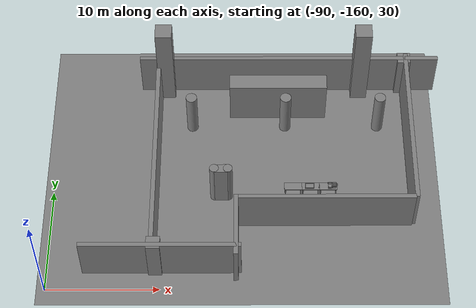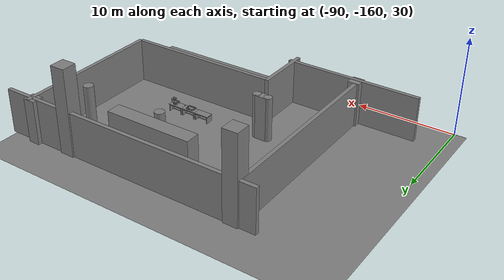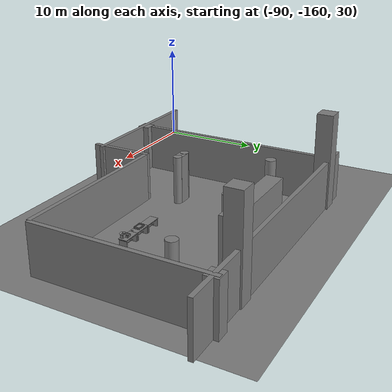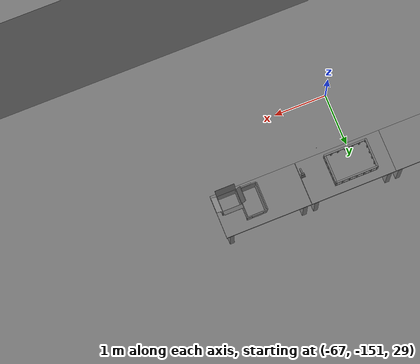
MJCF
<mujoco>
    <option gravity="0.000000000 0.000000000 -9.810000420" timestep="0.0049999999" integrator="implicitfast" density="1.225" viscosity="1.8000001e-05" noslip_iterations="10" iterations="100" sdf_iterations="50">
        <flag multiccd="disable"/>
    </option>
    <size memory="1000M"/>
    <compiler coordinate="local"/>
    <worldbody>
        <light cutoff="30" pos="0 1 1" dir="0 -1 -2"/>
        <light cutoff="30" pos="0 -1 1" dir="0 1 -2"/>
        <body pos="-64.866622925 -149.383972168 30.183746338" euler="89.999992371 89.999946594 0.000000000" name="openloong_gripper_2f85_fix_base_usda_bluebox_01">
            <geom contype="1" conaffinity="1" density="1000" type="box" material="" rgba="0.500000000 0.500000000 0.500000000 1.000000000" solimp="0.899999976 0.949999988 0.001000000" friction="1.000000000 0.005000000 0.000100000" solref="0.020000000 1.000000000" margin="0" condim="3" group="0" pos="0.276596069 0.187225342 0.000061035" quat="0.707107008 0.000077501 0.707106471 0.000077456" size="0.100000001 0.057999998 0.010000000" name="openloong_gripper_2f85_fix_base_usda_geom_5F7C389B_9DEE_4C1D_A8D6_0FAE427A52A5"/>
            <geom contype="1" conaffinity="1" density="1000" type="box" material="" rgba="0.500000000 0.500000000 0.500000000 1.000000000" solimp="0.899999976 0.949999988 0.001000000" friction="1.000000000 0.005000000 0.000100000" solref="0.020000000 1.000000000" margin="0" condim="3" group="0" pos="0.000000000 0.002883911 0.000000000" quat="1.000000000 0.000000000 0.000000000 0.000000000" size="0.254000008 0.003000000 0.172000006" name="openloong_gripper_2f85_fix_base_usda_geom_3CF1BCE5_33CF_4358_97FC_988E18EC662E"/>
            <geom contype="1" conaffinity="1" density="1000" type="box" material="" rgba="0.500000000 0.500000000 0.500000000 1.000000000" solimp="0.899999976 0.949999988 0.001000000" friction="1.000000000 0.005000000 0.000100000" solref="0.020000000 1.000000000" margin="0" condim="3" group="0" pos="0.000015259 0.124874115 0.173477173" quat="0.999796450 0.020176515 -0.000000015 0.000000030" size="0.259999990 0.119999997 0.007000000" name="openloong_gripper_2f85_fix_base_usda_geom_B18CD995_197C_4737_BB80_E73D9C0B5102"/>
            <geom contype="1" conaffinity="1" density="1000" type="box" material="" rgba="0.500000000 0.500000000 0.500000000 1.000000000" solimp="0.899999976 0.949999988 0.001000000" friction="1.000000000 0.005000000 0.000100000" solref="0.020000000 1.000000000" margin="0" condim="3" group="0" pos="0.000015259 0.124874115 -0.173477173" quat="0.999796450 -0.020176545 -0.000000015 0.000000000" size="0.259999990 0.119999997 0.007000000" name="openloong_gripper_2f85_fix_base_usda_geom_3FFD237E_4753_454D_92FF_0FCD297BE339"/>
            <geom contype="1" conaffinity="1" density="1000" type="box" material="" rgba="0.500000000 0.500000000 0.500000000 1.000000000" solimp="0.899999976 0.949999988 0.001000000" friction="1.000000000 0.005000000 0.000100000" solref="0.020000000 1.000000000" margin="0" condim="3" group="0" pos="0.000015259 0.214012146 0.188980103" quat="0.999913096 0.013176724 0.000000015 0.000000000" size="0.259999990 0.029999999 0.012500000" name="openloong_gripper_2f85_fix_base_usda_geom_8A4679EA_34A6_4C2A_B070_4EFEEAF813B9"/>
            <geom contype="1" conaffinity="1" density="1000" type="box" material="" rgba="0.500000000 0.500000000 0.500000000 1.000000000" solimp="0.899999976 0.949999988 0.001000000" friction="1.000000000 0.005000000 0.000100000" solref="0.020000000 1.000000000" margin="0" condim="3" group="0" pos="-0.258346558 0.125289917 0.001876831" quat="0.702796996 -0.020792052 0.710783184 0.020769238" size="0.189999998 0.119999997 0.009000000" name="openloong_gripper_2f85_fix_base_usda_geom_14DECBE8_83E2_4D19_AAFC_47B949941A5B"/>
            <geom contype="1" conaffinity="1" density="1000" type="box" material="" rgba="0.500000000 0.500000000 0.500000000 1.000000000" solimp="0.899999976 0.949999988 0.001000000" friction="1.000000000 0.005000000 0.000100000" solref="0.020000000 1.000000000" margin="0" condim="3" group="0" pos="0.000015259 0.214012146 -0.188980103" quat="0.999913096 -0.013176769 0.000000030 0.000000015" size="0.259999990 0.029999999 0.012500000" name="openloong_gripper_2f85_fix_base_usda_geom_2B7F5147_CD05_47F5_8662_F2CB919E0BC4"/>
            <geom contype="1" conaffinity="1" density="1000" type="box" material="" rgba="0.500000000 0.500000000 0.500000000 1.000000000" solimp="0.899999976 0.949999988 0.001000000" friction="1.000000000 0.005000000 0.000100000" solref="0.020000000 1.000000000" margin="0" condim="3" group="0" pos="-0.276596069 0.187225342 0.000061035" quat="0.707106650 0.000077441 0.707106709 0.000077456" size="0.100000001 0.057999998 0.010000000" name="openloong_gripper_2f85_fix_base_usda_geom_30B9B7A0_4CDE_4956_859C_2CDC351C4244"/>
            <geom contype="1" conaffinity="1" density="1000" type="box" material="" rgba="0.500000000 0.500000000 0.500000000 1.000000000" solimp="0.899999976 0.949999988 0.001000000" friction="1.000000000 0.005000000 0.000100000" solref="0.020000000 1.000000000" margin="0" condim="3" group="0" pos="0.258346558 0.125289917 0.001876831" quat="0.702851534 0.018856451 0.710823834 -0.019329429" size="0.189999998 0.119999997 0.009000000" name="openloong_gripper_2f85_fix_base_usda_geom_50675E1F_519F_4BDA_ABC1_81FB2E605B9B"/>
            <freejoint name="openloong_gripper_2f85_fix_base_usda_bluebox_01_joint"/>
            <site size="0.005000000 0.005000000 0.005000000" rgba="0.500000000 0.500000000 0.500000000 1.000000000" pos="0.000000000 0.000000000 0.000000000" quat="0.999961913 0.008726534 0.000000000 0.000000000" group="0" type="sphere" name="openloong_gripper_2f85_fix_base_usda_bluebox_01site"/>
        </body>
        <body pos="-64.496299744 -149.491867065 30.235729218" euler="0.000000000 0.000000000 89.999946594" name="openloong_gripper_2f85_fix_base_usda_cardboardbox_01">
            <geom contype="1" conaffinity="1" density="1000" type="box" material="" rgba="0.500000000 0.500000000 0.500000000 1.000000000" solimp="0.899999976 0.949999988 0.001000000" friction="1.000000000 0.005000000 0.000100000" solref="0.020000000 1.000000000" margin="0" condim="3" group="0" pos="-0.003166199 -0.004086494 0.005052090" quat="1.000000000 0.000000000 0.000000000 0.000000000" size="0.142499998 0.177500010 0.005000000" name="openloong_gripper_2f85_fix_base_usda_geom_5BD97F6B_E04F_46EF_BAA5_0867886BBB44"/>
            <geom contype="1" conaffinity="1" density="1000" type="box" material="" rgba="0.500000000 0.500000000 0.500000000 1.000000000" solimp="0.899999976 0.949999988 0.001000000" friction="1.000000000 0.005000000 0.000100000" solref="0.020000000 1.000000000" margin="0" condim="3" group="0" pos="-0.003166199 0.170316696 0.150570869" quat="1.000000000 0.000000000 0.000000000 0.000000000" size="0.142499998 0.005000000 0.149999991" name="openloong_gripper_2f85_fix_base_usda_geom_DCF5E314_A9DB_416B_BD20_31CC3BBFD647"/>
            <geom contype="1" conaffinity="1" density="1000" type="box" material="" rgba="0.500000000 0.500000000 0.500000000 1.000000000" solimp="0.899999976 0.949999988 0.001000000" friction="1.000000000 0.005000000 0.000100000" solref="0.020000000 1.000000000" margin="0" condim="3" group="0" pos="-0.147399902 -0.005307198 0.150570869" quat="1.000000000 0.000000000 0.000000000 0.000000000" size="0.005000000 0.177500010 0.149999991" name="openloong_gripper_2f85_fix_base_usda_geom_E78D93DC_79A0_487E_98C5_3ABA261409FA"/>
            <geom contype="1" conaffinity="1" density="1000" type="box" material="" rgba="0.500000000 0.500000000 0.500000000 1.000000000" solimp="0.899999976 0.949999988 0.001000000" friction="1.000000000 0.005000000 0.000100000" solref="0.020000000 1.000000000" margin="0" condim="3" group="0" pos="0.140275955 -0.005307198 0.150570869" quat="1.000000000 0.000000000 0.000000000 0.000000000" size="0.005000000 0.177500010 0.149999991" name="openloong_gripper_2f85_fix_base_usda_geom_51BFEC47_D1FD_4B71_87AE_BF863520BF93"/>
            <geom contype="1" conaffinity="1" density="1000" type="box" material="" rgba="0.500000000 0.500000000 0.500000000 1.000000000" solimp="0.899999976 0.949999988 0.001000000" friction="1.000000000 0.005000000 0.000100000" solref="0.020000000 1.000000000" margin="0" condim="3" group="0" pos="-0.003166199 -0.181550980 0.150570869" quat="1.000000000 0.000000000 0.000000000 0.000000000" size="0.142499998 0.005000000 0.149999991" name="openloong_gripper_2f85_fix_base_usda_geom_A695EE0A_E5A5_4510_83E0_7EC1D0471887"/>
            <freejoint name="openloong_gripper_2f85_fix_base_usda_cardboardbox_01_joint"/>
            <site size="0.005000000 0.005000000 0.005000000" rgba="0.500000000 0.500000000 0.500000000 1.000000000" pos="0.000000000 0.000000000 0.000000000" quat="0.999961913 0.008726535 0.000000000 0.000000000" group="0" type="sphere" name="openloong_gripper_2f85_fix_base_usda_site_B1E9A0D1_36A4_4A61_895C_9B6B24820911"/>
            <body pos="0.139160156 -0.004048347 0.301930904" euler="-179.999954224 49.383502960 179.999954224" name="openloong_gripper_2f85_fix_base_usda_A1_006">
                <geom contype="1" conaffinity="1" density="1000" type="box" material="" rgba="0.500000000 0.500000000 0.500000000 1.000000000" solimp="0.899999976 0.949999988 0.001000000" friction="1.000000000 0.005000000 0.000100000" solref="0.020000000 1.000000000" margin="0" condim="3" group="0" pos="-0.071587563 0.000009537 0.001745224" quat="0.999999881 0.000000000 0.000000000 0.000000000" size="0.071249999 0.179999992 0.002500000" name="openloong_gripper_2f85_fix_base_usda_geom_DD66336B_E82C_4DD1_85B3_63037420EAE4"/>
                <joint armature="0" stiffness="0.07" damping="0.0099999998" axis="0.000000 1.000000 0.000000" type="hinge" name="openloong_gripper_2f85_fix_base_usda_A1_006"/>
            </body>
            <body pos="-0.145902634 -0.004086494 0.301938057" euler="-180.000000000 -60.000011444 -180.000000000" name="openloong_gripper_2f85_fix_base_usda_A2_006">
                <geom contype="1" conaffinity="1" density="1000" type="box" material="" rgba="0.500000000 0.500000000 0.500000000 1.000000000" solimp="0.899999976 0.949999988 0.001000000" friction="1.000000000 0.005000000 0.000100000" solref="0.020000000 1.000000000" margin="0" condim="3" group="0" pos="0.071268082 0.000009537 0.002717972" quat="0.000002921 0.000000000 -0.000000030 0.999999881" size="0.071249999 0.179999992 0.002500000" name="openloong_gripper_2f85_fix_base_usda_geom_42E6C182_CC3A_4733_9026_F03314A05151"/>
                <joint armature="0" stiffness="0.07" damping="0.0099999998" axis="0.000000 1.000000 0.000000" type="hinge" name="openloong_gripper_2f85_fix_base_usda_A2_006"/>
            </body>
            <body pos="-0.003385544 0.175991058 0.301930904" euler="-125.858116150 -0.000004561 0.000002331" name="openloong_gripper_2f85_fix_base_usda_B2_006">
                <geom contype="1" conaffinity="1" density="1000" type="box" material="" rgba="0.500000000 0.500000000 0.500000000 1.000000000" solimp="0.899999976 0.949999988 0.001000000" friction="1.000000000 0.005000000 0.000100000" solref="0.020000000 1.000000000" margin="0" condim="3" group="0" pos="0.000009537 -0.070939064 -0.002470016" quat="0.999614120 0.027776197 -0.000000015 0.000000030" size="0.137500003 0.064999998 0.005000000" name="openloong_gripper_2f85_fix_base_usda_geom_D0CE304F_B080_47B5_90AC_2502A781BDEC"/>
                <joint armature="0" stiffness="0.07" damping="0.0099999998" axis="1.000000 0.000000 0.000000" type="hinge" name="openloong_gripper_2f85_fix_base_usda_B2_006"/>
            </body>
            <body pos="-0.003385544 -0.184140205 0.301938057" euler="147.805557251 0.000000000 0.000000000" name="openloong_gripper_2f85_fix_base_usda_B1_006">
                <geom contype="1" conaffinity="1" density="1000" type="box" material="" rgba="0.500000000 0.500000000 0.500000000 1.000000000" solimp="0.899999976 0.949999988 0.001000000" friction="1.000000000 0.005000000 0.000100000" solref="0.020000000 1.000000000" margin="0" condim="3" group="0" pos="-0.000028610 0.070202351 -0.002703667" quat="0.999614179 -0.027776167 0.000000000 0.000000000" size="0.137500003 0.064999998 0.005000000" name="openloong_gripper_2f85_fix_base_usda_geom_25E3EF0F_1AA2_4CC2_B988_5CB50161F25C"/>
                <joint armature="0" stiffness="0.07" damping="0.0099999998" axis="1.000000 0.000000 0.000000" type="hinge" name="openloong_gripper_2f85_fix_base_usda_B1_006"/>
            </body>
        </body>
        <body pos="-65.882858276 -149.481979370 30.229999542" euler="-64.487716675 0.000000000 0.000000000" name="openloong_gripper_2f85_fix_base_usda_Barcode">
            <geom contype="1" conaffinity="1" density="1000" type="box" material="" rgba="0.500000000 0.500000000 0.500000000 1.000000000" solimp="0.899999976 0.949999988 0.001000000" friction="1.000000000 0.005000000 0.000100000" solref="0.020000000 1.000000000" margin="0" condim="3" group="0" pos="0.000000000 0.013038635 0.001419067" quat="0.000000000 0.000000000 0.000000000 1.000000119" size="0.034000002 0.010000000 0.017999999" name="openloong_gripper_2f85_fix_base_usda_geom_773B2CD1_ADE1_44C0_BDA2_6E4CF5F40DF4"/>
            <geom contype="1" conaffinity="1" density="1000" type="box" material="" rgba="0.500000000 0.500000000 0.500000000 1.000000000" solimp="0.899999976 0.949999988 0.001000000" friction="1.000000000 0.005000000 0.000100000" solref="0.020000000 1.000000000" margin="0" condim="3" group="0" pos="0.000000000 -0.035301208 -0.007095337" quat="0.000000000 0.000000000 -0.043619365 0.999048233" size="0.028999999 0.010000000 0.020000000" name="openloong_gripper_2f85_fix_base_usda_geom_5800FDEC_F3F4_412B_9510_534AF38E604D"/>
            <geom contype="1" conaffinity="1" density="1000" type="box" material="" rgba="0.500000000 0.500000000 0.500000000 1.000000000" solimp="0.899999976 0.949999988 0.001000000" friction="1.000000000 0.005000000 0.000100000" solref="0.020000000 1.000000000" margin="0" condim="3" group="0" pos="0.000000000 -0.043411255 -0.011749268" quat="0.922262907 0.386563420 0.000000000 0.000000000" size="0.026000001 0.010000000 0.020000000" name="openloong_gripper_2f85_fix_base_usda_geom_10C73365_E3E6_4CF5_8A7A_86D990AABF77"/>
            <geom contype="1" conaffinity="1" density="1000" type="box" material="" rgba="0.500000000 0.500000000 0.500000000 1.000000000" solimp="0.899999976 0.949999988 0.001000000" friction="1.000000000 0.005000000 0.000100000" solref="0.020000000 1.000000000" margin="0" condim="3" group="0" pos="0.000000000 -0.016967773 -0.031860352" quat="0.000000000 0.000000000 0.000000000 1.000000119" size="0.008000000 0.010000000 0.013000000" name="openloong_gripper_2f85_fix_base_usda_geom_B6F2E202_4E49_4D9D_91F5_094876A23EE6"/>
            <geom contype="1" conaffinity="1" density="1000" type="box" material="" rgba="0.500000000 0.500000000 0.500000000 1.000000000" solimp="0.899999976 0.949999988 0.001000000" friction="1.000000000 0.005000000 0.000100000" solref="0.020000000 1.000000000" margin="0" condim="3" group="0" pos="0.000000000 -0.001869202 0.000312805" quat="0.953716993 0.300705761 0.000000000 0.000000000" size="0.032000002 0.010000000 0.018999999" name="openloong_gripper_2f85_fix_base_usda_geom_CE1C20C7_14CA_4F74_81EC_6350BCB49267"/>
            <geom contype="1" conaffinity="1" density="1000" type="box" material="" rgba="0.500000000 0.500000000 0.500000000 1.000000000" solimp="0.899999976 0.949999988 0.001000000" friction="1.000000000 0.005000000 0.000100000" solref="0.020000000 1.000000000" margin="0" condim="3" group="0" pos="0.000000000 -0.019531250 -0.003173828" quat="0.953716993 0.300705761 0.000000000 0.000000000" size="0.030999999 0.010000000 0.020000000" name="openloong_gripper_2f85_fix_base_usda_geom_FC239A51_F613_4E9E_B267_7F31C16E862C"/>
            <geom contype="1" conaffinity="1" density="1000" type="box" material="" rgba="0.500000000 0.500000000 0.500000000 1.000000000" solimp="0.899999976 0.949999988 0.001000000" friction="1.000000000 0.005000000 0.000100000" solref="0.020000000 1.000000000" margin="0" condim="3" group="0" pos="0.000000000 -0.035301208 -0.007095337" quat="0.953716993 0.300705761 0.000000000 0.000000000" size="0.028999999 0.010000000 0.020000000" name="openloong_gripper_2f85_fix_base_usda_geom_E8B31071_913D_4477_A605_97C11A6E23D0"/>
            <geom contype="1" conaffinity="1" density="1000" type="box" material="" rgba="0.500000000 0.500000000 0.500000000 1.000000000" solimp="0.899999976 0.949999988 0.001000000" friction="1.000000000 0.005000000 0.000100000" solref="0.020000000 1.000000000" margin="0" condim="3" group="0" pos="0.000000000 -0.042617798 -0.071121216" quat="0.000000000 0.000000000 0.000000000 1.000000119" size="0.013000000 0.021000000 0.059999999" name="openloong_gripper_2f85_fix_base_usda_geom_82920AFE_4159_4E1D_A540_AE943134BF31"/>
            <freejoint name="openloong_gripper_2f85_fix_base_usda_Barcode_joint"/>
            <site size="0.005000000 0.005000000 0.005000000" rgba="0.500000000 0.500000000 0.500000000 1.000000000" pos="0.000000000 0.000000000 0.000000000" quat="1.000000000 0.000000000 0.000000000 0.000000000" group="0" type="sphere" name="openloong_gripper_2f85_fix_base_usda_Barcode_site"/>
        </body>
        <body pos="-66.745018005 -149.392349243 30.184000015" euler="0.000000000 0.000000000 89.999946594" name="[22331170524766]_Basket_01">
            <geom contype="1" conaffinity="1" density="1000" type="box" material="" rgba="0.500000000 0.500000000 0.500000000 1.000000000" solimp="0.899999976 0.949999988 0.001000000" friction="1.000000000 0.005000000 0.000100000" solref="0.020000000 1.000000000" margin="0" condim="3" group="0" pos="-0.052425385 0.389207840 0.089787483" quat="0.707107008 0.000000000 0.000000000 0.707106411" size="0.014249999 0.014249999 0.059999999" name="[22331170524766]_geom_27B0C0D5_B844_466F_830A_8808E70B28FF"/>
            <geom contype="1" conaffinity="1" density="1000" type="box" material="" rgba="0.500000000 0.500000000 0.500000000 1.000000000" solimp="0.899999976 0.949999988 0.001000000" friction="1.000000000 0.005000000 0.000100000" solref="0.020000000 1.000000000" margin="0" condim="3" group="0" pos="0.264015198 -0.133043289 0.089787483" quat="0.707107008 0.000000000 0.000000000 0.707106411" size="0.014249999 0.014249999 0.059999999" name="[22331170524766]_geom_AC6C6C6A_BE43_4FFE_AF24_307CB1A99F5B"/>
            <geom contype="1" conaffinity="1" density="1000" type="box" material="" rgba="0.500000000 0.500000000 0.500000000 1.000000000" solimp="0.899999976 0.949999988 0.001000000" friction="1.000000000 0.005000000 0.000100000" solref="0.020000000 1.000000000" margin="0" condim="3" group="0" pos="-0.264015198 -0.265548706 0.089793205" quat="0.707107008 0.000000000 0.000000000 0.707106411" size="0.014249999 0.014249999 0.059999999" name="[22331170524766]_geom_E0B5F902_73D4_490D_95CF_63BCB40D87B3"/>
            <geom contype="1" conaffinity="1" density="1000" type="box" material="" rgba="0.500000000 0.500000000 0.500000000 1.000000000" solimp="0.899999976 0.949999988 0.001000000" friction="1.000000000 0.005000000 0.000100000" solref="0.020000000 1.000000000" margin="0" condim="3" group="0" pos="-0.160263062 -0.389322281 0.089793205" quat="0.707107008 0.000000000 0.000000000 0.707106411" size="0.014249999 0.014249999 0.059999999" name="[22331170524766]_geom_AA72EB6C_5E41_4B4D_892F_1DCCC66720FA"/>
            <geom contype="1" conaffinity="1" density="1000" type="box" material="" rgba="0.500000000 0.500000000 0.500000000 1.000000000" solimp="0.899999976 0.949999988 0.001000000" friction="1.000000000 0.005000000 0.000100000" solref="0.020000000 1.000000000" margin="0" condim="3" group="0" pos="0.162265778 -0.389322281 0.089787483" quat="0.707107008 0.000000000 0.000000000 0.707106411" size="0.014249999 0.014249999 0.059999999" name="[22331170524766]_geom_A0C150F3_1983_4D99_9858_2993C14D676F"/>
            <geom contype="1" conaffinity="1" density="1000" type="box" material="" rgba="0.500000000 0.500000000 0.500000000 1.000000000" solimp="0.899999976 0.949999988 0.001000000" friction="1.000000000 0.005000000 0.000100000" solref="0.020000000 1.000000000" margin="0" condim="3" group="0" pos="0.264015198 0.389207840 0.089787483" quat="0.707107008 0.000000000 0.000000000 0.707106411" size="0.014249999 0.014249999 0.059999999" name="[22331170524766]_geom_2D928DB9_D8F3_4187_B712_A190AE9F4899"/>
            <geom contype="1" conaffinity="1" density="1000" type="box" material="" rgba="0.500000000 0.500000000 0.500000000 1.000000000" solimp="0.899999976 0.949999988 0.001000000" friction="1.000000000 0.005000000 0.000100000" solref="0.020000000 1.000000000" margin="0" condim="3" group="0" pos="-0.264015198 -0.133043289 0.089793205" quat="0.707107008 0.000000000 0.000000000 0.707106411" size="0.014249999 0.014249999 0.059999999" name="[22331170524766]_geom_B7F6E0FF_4CE3_44DE_8647_672951455499"/>
            <geom contype="1" conaffinity="1" density="1000" type="box" material="" rgba="0.500000000 0.500000000 0.500000000 1.000000000" solimp="0.899999976 0.949999988 0.001000000" friction="1.000000000 0.005000000 0.000100000" solref="0.020000000 1.000000000" margin="0" condim="3" group="0" pos="-0.264026642 0.269256592 0.089793205" quat="0.707107008 0.000000000 0.000000000 0.707106411" size="0.014249999 0.014249999 0.059999999" name="[22331170524766]_geom_943D5440_A1A4_4E95_B00A_5252ABE4AADA"/>
            <geom contype="1" conaffinity="1" density="1000" type="box" material="" rgba="0.500000000 0.500000000 0.500000000 1.000000000" solimp="0.899999976 0.949999988 0.001000000" friction="1.000000000 0.005000000 0.000100000" solref="0.020000000 1.000000000" margin="0" condim="3" group="0" pos="0.054462433 0.389207840 0.089787483" quat="0.707107008 0.000000000 0.000000000 0.707106411" size="0.014249999 0.014249999 0.059999999" name="[22331170524766]_geom_1D6676A0_3DE2_45E7_B3F9_644545D8166A"/>
            <geom contype="1" conaffinity="1" density="1000" type="box" material="" rgba="0.500000000 0.500000000 0.500000000 1.000000000" solimp="0.899999976 0.949999988 0.001000000" friction="1.000000000 0.005000000 0.000100000" solref="0.020000000 1.000000000" margin="0" condim="3" group="0" pos="0.054462433 -0.389322281 0.089787483" quat="0.707107008 0.000000000 0.000000000 0.707106411" size="0.014249999 0.014249999 0.059999999" name="[22331170524766]_geom_3D0D2ECC_070B_45F1_AB32_E56DA76D1543"/>
            <geom contype="1" conaffinity="1" density="1000" type="box" material="" rgba="0.500000000 0.500000000 0.500000000 1.000000000" solimp="0.899999976 0.949999988 0.001000000" friction="1.000000000 0.005000000 0.000100000" solref="0.020000000 1.000000000" margin="0" condim="3" group="0" pos="0.264015198 0.269256592 0.089793205" quat="0.707107008 0.000000000 0.000000000 0.707106411" size="0.014249999 0.014249999 0.059999999" name="[22331170524766]_geom_5EBB71B6_6898_4F97_B677_FC5C8082FCAB"/>
            <geom contype="1" conaffinity="1" density="1000" type="box" material="" rgba="0.500000000 0.500000000 0.500000000 1.000000000" solimp="0.899999976 0.949999988 0.001000000" friction="1.000000000 0.005000000 0.000100000" solref="0.020000000 1.000000000" margin="0" condim="3" group="0" pos="0.264015198 -0.389322281 0.089787483" quat="0.707107008 0.000000000 0.000000000 0.707106411" size="0.014249999 0.014249999 0.059999999" name="[22331170524766]_geom_DA0EAE89_E071_4E14_A6B6_5BFC4D1E6C34"/>
            <geom contype="1" conaffinity="1" density="1000" type="box" material="" rgba="0.500000000 0.500000000 0.500000000 1.000000000" solimp="0.899999976 0.949999988 0.001000000" friction="1.000000000 0.005000000 0.000100000" solref="0.020000000 1.000000000" margin="0" condim="3" group="0" pos="0.000000000 0.000000000 0.015998840" quat="0.707107008 0.000000000 0.000000000 0.707106411" size="0.403499991 0.279000014 0.015750000" name="[22331170524766]_geom_4B7735B4_7EA2_49A3_8F20_E7A7B77B410B"/>
            <geom contype="1" conaffinity="1" density="1000" type="box" material="" rgba="0.500000000 0.500000000 0.500000000 1.000000000" solimp="0.899999976 0.949999988 0.001000000" friction="1.000000000 0.005000000 0.000100000" solref="0.020000000 1.000000000" margin="0" condim="3" group="0" pos="0.000000000 -0.389476776 0.163619041" quat="0.707107008 0.000000000 0.000000000 0.707106411" size="0.015000000 0.277500004 0.015750000" name="[22331170524766]_geom_5FFEEA09_8105_4C1E_A7A4_0C0004A6116F"/>
            <geom contype="1" conaffinity="1" density="1000" type="box" material="" rgba="0.500000000 0.500000000 0.500000000 1.000000000" solimp="0.899999976 0.949999988 0.001000000" friction="1.000000000 0.005000000 0.000100000" solref="0.020000000 1.000000000" margin="0" condim="3" group="0" pos="0.162265778 0.389207840 0.089787483" quat="0.707107008 0.000000000 0.000000000 0.707106411" size="0.014249999 0.014249999 0.059999999" name="[22331170524766]_geom_3BBFF40C_9926_4549_B20D_94B818B4DA80"/>
            <geom contype="1" conaffinity="1" density="1000" type="box" material="" rgba="0.500000000 0.500000000 0.500000000 1.000000000" solimp="0.899999976 0.949999988 0.001000000" friction="1.000000000 0.005000000 0.000100000" solref="0.020000000 1.000000000" margin="0" condim="3" group="0" pos="0.000000000 0.389471054 0.163619041" quat="0.707107008 0.000000000 0.000000000 0.707106411" size="0.015000000 0.277500004 0.015750000" name="[22331170524766]_geom_A6E14767_B5A6_41FB_9471_2ED7560811DF"/>
            <geom contype="1" conaffinity="1" density="1000" type="box" material="" rgba="0.500000000 0.500000000 0.500000000 1.000000000" solimp="0.899999976 0.949999988 0.001000000" friction="1.000000000 0.005000000 0.000100000" solref="0.020000000 1.000000000" margin="0" condim="3" group="0" pos="-0.263511658 0.000000000 0.163619041" quat="0.707107008 0.000000000 0.000000000 0.707106411" size="0.403499991 0.015000000 0.015750000" name="[22331170524766]_geom_4BBB122E_30B8_44F8_AD21_04A104480D65"/>
            <geom contype="1" conaffinity="1" density="1000" type="box" material="" rgba="0.500000000 0.500000000 0.500000000 1.000000000" solimp="0.899999976 0.949999988 0.001000000" friction="1.000000000 0.005000000 0.000100000" solref="0.020000000 1.000000000" margin="0" condim="3" group="0" pos="-0.264015198 0.141334534 0.089793205" quat="0.707107008 0.000000000 0.000000000 0.707106411" size="0.014249999 0.014249999 0.059999999" name="[22331170524766]_geom_8D7AB4E2_0BF0_4DDE_9F2C_630B0229C519"/>
            <geom contype="1" conaffinity="1" density="1000" type="box" material="" rgba="0.500000000 0.500000000 0.500000000 1.000000000" solimp="0.899999976 0.949999988 0.001000000" friction="1.000000000 0.005000000 0.000100000" solref="0.020000000 1.000000000" margin="0" condim="3" group="0" pos="0.264015198 -0.265548706 0.089787483" quat="0.707107008 0.000000000 0.000000000 0.707106411" size="0.014249999 0.014249999 0.059999999" name="[22331170524766]_geom_00B3A005_88E4_4FA7_91D8_F22B9BC40E20"/>
            <geom contype="1" conaffinity="1" density="1000" type="box" material="" rgba="0.500000000 0.500000000 0.500000000 1.000000000" solimp="0.899999976 0.949999988 0.001000000" friction="1.000000000 0.005000000 0.000100000" solref="0.020000000 1.000000000" margin="0" condim="3" group="0" pos="-0.160263062 0.389207840 0.089787483" quat="0.707107008 0.000000000 0.000000000 0.707106411" size="0.014249999 0.014249999 0.059999999" name="[22331170524766]_geom_8B1CAB38_39C4_4ACF_B710_860D3E1297F6"/>
            <geom contype="1" conaffinity="1" density="1000" type="box" material="" rgba="0.500000000 0.500000000 0.500000000 1.000000000" solimp="0.899999976 0.949999988 0.001000000" friction="1.000000000 0.005000000 0.000100000" solref="0.020000000 1.000000000" margin="0" condim="3" group="0" pos="-0.052425385 -0.389322281 0.089787483" quat="0.707107008 0.000000000 0.000000000 0.707106411" size="0.014249999 0.014249999 0.059999999" name="[22331170524766]_geom_F8B30AEA_0B9C_4F02_BBE5_D70DD835CB78"/>
            <geom contype="1" conaffinity="1" density="1000" type="box" material="" rgba="0.500000000 0.500000000 0.500000000 1.000000000" solimp="0.899999976 0.949999988 0.001000000" friction="1.000000000 0.005000000 0.000100000" solref="0.020000000 1.000000000" margin="0" condim="3" group="0" pos="-0.264026642 -0.389322281 0.089793205" quat="0.707107008 0.000000000 0.000000000 0.707106411" size="0.014249999 0.014249999 0.059999999" name="[22331170524766]_geom_95D6B452_8636_441A_9CA8_15A0AA825722"/>
            <geom contype="1" conaffinity="1" density="1000" type="box" material="" rgba="0.500000000 0.500000000 0.500000000 1.000000000" solimp="0.899999976 0.949999988 0.001000000" friction="1.000000000 0.005000000 0.000100000" solref="0.020000000 1.000000000" margin="0" condim="3" group="0" pos="0.264015198 0.141334534 0.089787483" quat="0.707107008 0.000000000 0.000000000 0.707106411" size="0.014249999 0.014249999 0.059999999" name="[22331170524766]_geom_4F30006D_6ED9_42BB_AEE3_0D4BB4938D7B"/>
            <geom contype="1" conaffinity="1" density="1000" type="box" material="" rgba="0.500000000 0.500000000 0.500000000 1.000000000" solimp="0.899999976 0.949999988 0.001000000" friction="1.000000000 0.005000000 0.000100000" solref="0.020000000 1.000000000" margin="0" condim="3" group="0" pos="-0.264015198 0.389207840 0.089793205" quat="0.707107008 0.000000000 0.000000000 0.707106411" size="0.014249999 0.014249999 0.059999999" name="[22331170524766]_geom_F32041D9_7E07_443F_8364_76CD565064E5"/>
            <geom contype="1" conaffinity="1" density="1000" type="box" material="" rgba="0.500000000 0.500000000 0.500000000 1.000000000" solimp="0.899999976 0.949999988 0.001000000" friction="1.000000000 0.005000000 0.000100000" solref="0.020000000 1.000000000" margin="0" condim="3" group="0" pos="0.264015198 0.004480362 0.089787483" quat="0.707107008 0.000000000 0.000000000 0.707106411" size="0.014249999 0.014249999 0.059999999" name="[22331170524766]_geom_37AC43C5_2ECA_4C44_8317_15C9FB83B864"/>
            <geom contype="1" conaffinity="1" density="1000" type="box" material="" rgba="0.500000000 0.500000000 0.500000000 1.000000000" solimp="0.899999976 0.949999988 0.001000000" friction="1.000000000 0.005000000 0.000100000" solref="0.020000000 1.000000000" margin="0" condim="3" group="0" pos="0.263694763 -0.000011444 0.163619041" quat="0.707107008 0.000000000 0.000000000 0.707106411" size="0.403499991 0.015000000 0.015750000" name="[22331170524766]_geom_5F398430_21F1_44AD_88A3_E17EA318425A"/>
            <geom contype="1" conaffinity="1" density="1000" type="box" material="" rgba="0.500000000 0.500000000 0.500000000 1.000000000" solimp="0.899999976 0.949999988 0.001000000" friction="1.000000000 0.005000000 0.000100000" solref="0.020000000 1.000000000" margin="0" condim="3" group="0" pos="-0.264015198 0.004480362 0.089793205" quat="0.707107008 0.000000000 0.000000000 0.707106411" size="0.014249999 0.014249999 0.059999999" name="[22331170524766]_geom_155AABF5_3B75_4A83_ADEB_8EAF13EDB0C9"/>
            <freejoint name="[22331170524766]_joint_35C3478D_2BE4_405F_BFD9_2C833F703CAE"/>
        </body>
        <body pos="0.000000000 0.000000000 0.000000000" euler="0.000000000 0.000000000 0.000000000" name="Static Objects_Static Objects">
            <geom contype="1" conaffinity="1" density="1000" type="box" material="" rgba="0.500000000 0.500000000 0.500000000 1.000000000" solimp="0.899999976 0.949999988 0.001000000" friction="1.000000000 0.005000000 0.000100000" solref="0.020000000 1.000000000" margin="0" condim="3" group="0" pos="-67.544113159 -149.365814209 29.727830887" quat="0.500000417 0.499999970 0.499999553 0.499999970" size="0.381000012 0.319999993 0.041000001" name="Static Objects_geom_77F4782C_7907_4378_8DA0_9CF8E36978CF"/>
            <geom contype="1" conaffinity="1" density="1000" type="box" material="" rgba="0.500000000 0.500000000 0.500000000 1.000000000" solimp="0.899999976 0.949999988 0.001000000" friction="1.000000000 0.005000000 0.000100000" solref="0.020000000 1.000000000" margin="0" condim="3" group="0" pos="-68.239501953 -149.365814209 30.086868286" quat="0.500000417 0.499999970 0.499999553 0.499999970" size="0.370999992 0.039500002 0.745000005" name="Static Objects_geom_585093B4_834D_45D1_B9C3_2B14BD4FB06B"/>
            <geom contype="1" conaffinity="1" density="1000" type="box" material="" rgba="0.500000000 0.500000000 0.500000000 1.000000000" solimp="0.899999976 0.949999988 0.001000000" friction="1.000000000 0.005000000 0.000100000" solref="0.020000000 1.000000000" margin="0" condim="3" group="0" pos="-68.239501953 -149.365814209 30.147235870" quat="0.500000417 0.499999970 0.499999553 0.499999970" size="0.400000006 0.022000000 0.800000012" name="Static Objects_geom_50983C48_76D9_4622_AEAD_8B5AA2D3226F"/>
            <geom contype="1" conaffinity="1" density="1000" type="box" material="" rgba="0.500000000 0.500000000 0.500000000 1.000000000" solimp="0.899999976 0.949999988 0.001000000" friction="1.000000000 0.005000000 0.000100000" solref="0.020000000 1.000000000" margin="0" condim="3" group="0" pos="-68.934890747 -149.365814209 29.727830887" quat="0.500000417 0.499999970 0.499999553 0.499999970" size="0.381000012 0.319999993 0.041000001" name="Static Objects_geom_30835E13_E9BF_47B7_8D60_B38BC07CDA6F"/>
            <geom contype="1" conaffinity="1" density="1000" type="box" material="" rgba="0.500000000 0.500000000 0.500000000 1.000000000" solimp="0.899999976 0.949999988 0.001000000" friction="1.000000000 0.005000000 0.000100000" solref="0.020000000 1.000000000" margin="0" condim="3" group="0" pos="-68.239501953 -149.365814209 29.561563492" quat="0.500000417 0.499999970 0.499999553 0.499999970" size="0.020000000 0.022000000 0.660000026" name="Static Objects_geom_AFA5222B_B780_4459_8C98_E1F472414759"/>
            <geom contype="1" conaffinity="1" density="1000" type="box" material="" rgba="0.500000000 0.500000000 0.500000000 1.000000000" solimp="0.899999976 0.949999988 0.001000000" friction="1.000000000 0.005000000 0.000100000" solref="0.020000000 1.000000000" margin="0" condim="3" group="0" pos="-65.945671082 -149.365814209 29.727830887" quat="0.500000417 0.499999970 0.499999553 0.499999970" size="0.381000012 0.319999993 0.041000001" name="Static Objects_geom_06A271C4_A0FD_4DC7_B5B4_A6FDB3A37E95"/>
            <geom contype="1" conaffinity="1" density="1000" type="box" material="" rgba="0.500000000 0.500000000 0.500000000 1.000000000" solimp="0.899999976 0.949999988 0.001000000" friction="1.000000000 0.005000000 0.000100000" solref="0.020000000 1.000000000" margin="0" condim="3" group="0" pos="-66.641059875 -149.365814209 30.086868286" quat="0.500000417 0.499999970 0.499999553 0.499999970" size="0.370999992 0.039500002 0.745000005" name="Static Objects_geom_0B5D45C0_8CB7_48C1_B994_2E72842DAE0F"/>
            <geom contype="1" conaffinity="1" density="1000" type="box" material="" rgba="0.500000000 0.500000000 0.500000000 1.000000000" solimp="0.899999976 0.949999988 0.001000000" friction="1.000000000 0.005000000 0.000100000" solref="0.020000000 1.000000000" margin="0" condim="3" group="0" pos="-66.641059875 -149.365814209 30.147235870" quat="0.500000417 0.499999970 0.499999553 0.499999970" size="0.400000006 0.022000000 0.800000012" name="Static Objects_geom_26C5C607_87E5_47EE_B320_BD6E0C5940B1"/>
            <geom contype="1" conaffinity="1" density="1000" type="box" material="" rgba="0.500000000 0.500000000 0.500000000 1.000000000" solimp="0.899999976 0.949999988 0.001000000" friction="1.000000000 0.005000000 0.000100000" solref="0.020000000 1.000000000" margin="0" condim="3" group="0" pos="-67.336448669 -149.365814209 29.727830887" quat="0.500000417 0.499999970 0.499999553 0.499999970" size="0.381000012 0.319999993 0.041000001" name="Static Objects_geom_B24BA450_632B_4880_BDCC_1FF126B35CAE"/>
            <geom contype="1" conaffinity="1" density="1000" type="box" material="" rgba="0.500000000 0.500000000 0.500000000 1.000000000" solimp="0.899999976 0.949999988 0.001000000" friction="1.000000000 0.005000000 0.000100000" solref="0.020000000 1.000000000" margin="0" condim="3" group="0" pos="-66.641059875 -149.365814209 29.561563492" quat="0.500000417 0.499999970 0.499999553 0.499999970" size="0.020000000 0.022000000 0.660000026" name="Static Objects_geom_E2509577_335B_4015_838F_5B4C3987A082"/>
            <geom contype="1" conaffinity="1" density="1000" type="box" material="" rgba="0.500000000 0.500000000 0.500000000 1.000000000" solimp="0.899999976 0.949999988 0.001000000" friction="1.000000000 0.005000000 0.000100000" solref="0.020000000 1.000000000" margin="0" condim="3" group="0" pos="-64.338577271 -149.365814209 29.727830887" quat="0.500000417 0.499999970 0.499999553 0.499999970" size="0.381000012 0.319999993 0.041000001" name="Static Objects_geom_672B55E2_41AD_4D6E_988C_AF39FBC8D277"/>
            <geom contype="1" conaffinity="1" density="1000" type="box" material="" rgba="0.500000000 0.500000000 0.500000000 1.000000000" solimp="0.899999976 0.949999988 0.001000000" friction="1.000000000 0.005000000 0.000100000" solref="0.020000000 1.000000000" margin="0" condim="3" group="0" pos="-65.033966064 -149.365814209 30.086868286" quat="0.500000417 0.499999970 0.499999553 0.499999970" size="0.370999992 0.039500002 0.745000005" name="Static Objects_geom_B763A26D_F2AD_41CF_BE07_0078F8B00D01"/>
            <geom contype="1" conaffinity="1" density="1000" type="box" material="" rgba="0.500000000 0.500000000 0.500000000 1.000000000" solimp="0.899999976 0.949999988 0.001000000" friction="1.000000000 0.005000000 0.000100000" solref="0.020000000 1.000000000" margin="0" condim="3" group="0" pos="-65.033966064 -149.365814209 30.147235870" quat="0.500000417 0.499999970 0.499999553 0.499999970" size="0.400000006 0.022000000 0.800000012" name="Static Objects_geom_6A1EE0A0_8E68_4DB3_9CE9_E773DCFEDFAB"/>
            <geom contype="1" conaffinity="1" density="1000" type="box" material="" rgba="0.500000000 0.500000000 0.500000000 1.000000000" solimp="0.899999976 0.949999988 0.001000000" friction="1.000000000 0.005000000 0.000100000" solref="0.020000000 1.000000000" margin="0" condim="3" group="0" pos="-65.729354858 -149.365814209 29.727830887" quat="0.500000417 0.499999970 0.499999553 0.499999970" size="0.381000012 0.319999993 0.041000001" name="Static Objects_geom_7A987E11_7E38_452C_BEFA_D71868566B56"/>
            <geom contype="1" conaffinity="1" density="1000" type="box" material="" rgba="0.500000000 0.500000000 0.500000000 1.000000000" solimp="0.899999976 0.949999988 0.001000000" friction="1.000000000 0.005000000 0.000100000" solref="0.020000000 1.000000000" margin="0" condim="3" group="0" pos="-65.033966064 -149.365814209 29.561563492" quat="0.500000417 0.499999970 0.499999553 0.499999970" size="0.020000000 0.022000000 0.660000026" name="Static Objects_geom_22966189_9AD5_42EF_9A45_293FB5D9AFCA"/>
            <geom contype="1" conaffinity="1" density="1000" type="box" material="" rgba="0.500000000 0.500000000 0.500000000 1.000000000" solimp="0.899999976 0.949999988 0.001000000" friction="1.000000000 0.005000000 0.000100000" solref="0.020000000 1.000000000" margin="0" condim="3" group="0" pos="-61.754566193 -137.853729248 33.906845093" quat="0.707107067 0.000000000 0.000000000 0.707106471" size="0.759999990 0.759999990 4.500000000" name="Static Objects_geom_FD44F3C4_5445_4DCB_8CB4_135362FA923A"/>
            <geom contype="1" conaffinity="1" density="1000" type="box" material="" rgba="0.500000000 0.500000000 0.500000000 1.000000000" solimp="0.899999976 0.949999988 0.001000000" friction="1.000000000 0.005000000 0.000100000" solref="0.020000000 1.000000000" margin="0" condim="3" group="0" pos="-57.511135101 -144.927108765 31.707921982" quat="1.000000000 0.000000000 0.000000000 0.000000000" size="0.200000003 8.000000000 2.299999952" name="Static Objects_geom_993541A2_1796_4ACD_A591_62908287876D"/>
            <geom contype="1" conaffinity="1" density="1000" type="box" material="" rgba="0.500000000 0.500000000 0.500000000 1.000000000" solimp="0.899999976 0.949999988 0.001000000" friction="1.000000000 0.005000000 0.000100000" solref="0.020000000 1.000000000" margin="0" condim="3" group="0" pos="-80.517646790 -157.574050903 31.688196182" quat="0.707107067 0.000000000 0.000000000 0.707106471" size="0.600000024 0.600000024 2.299999952" name="Static Objects_geom_F5B6032A_9E9A_44B4_93E6_12EFFAEA55F6"/>
            <geom contype="1" conaffinity="1" density="1000" type="box" material="" rgba="0.500000000 0.500000000 0.500000000 1.000000000" solimp="0.899999976 0.949999988 0.001000000" friction="1.000000000 0.005000000 0.000100000" solref="0.020000000 1.000000000" margin="0" condim="3" group="0" pos="-80.711044312 -147.414932251 31.666158676" quat="1.000000000 0.000000000 0.000000000 0.000000000" size="0.200000003 10.000000000 2.299999952" name="Static Objects_geom_6598391E_BAB8_43D4_AE9E_93104C1AF0E1"/>
            <geom contype="1" conaffinity="1" density="1000" type="box" material="" rgba="0.500000000 0.500000000 0.500000000 1.000000000" solimp="0.899999976 0.949999988 0.001000000" friction="1.000000000 0.005000000 0.000100000" solref="0.020000000 1.000000000" margin="0" condim="3" group="0" pos="-57.687217712 -137.434692383 31.688196182" quat="0.707107067 0.000000000 0.000000000 0.707106471" size="0.600000024 0.600000024 2.299999952" name="Static Objects_geom_300D23B2_8803_4336_A8A6_6B950A482B06"/>
            <geom contype="1" conaffinity="1" density="1000" type="box" material="" rgba="0.500000000 0.500000000 0.500000000 1.000000000" solimp="0.899999976 0.949999988 0.001000000" friction="1.000000000 0.005000000 0.000100000" solref="0.020000000 1.000000000" margin="0" condim="3" group="0" pos="-69.537033081 -140.263229370 31.714921951" quat="0.707107067 0.000000000 0.000000000 0.707106471" size="0.759999990 4.500000000 2.299999952" name="Static Objects_geom_CFBF7B9C_5DDA_49C4_8DFB_0BE93450DB57"/>
            <geom contype="1" conaffinity="1" density="1000" type="box" material="" rgba="0.500000000 0.500000000 0.500000000 1.000000000" solimp="0.899999976 0.949999988 0.001000000" friction="1.000000000 0.005000000 0.000100000" solref="0.020000000 1.000000000" margin="0" condim="3" group="0" pos="-80.073638916 -137.853713989 33.906845093" quat="0.707107067 0.000000000 0.000000000 0.707106471" size="0.759999990 0.759999990 4.500000000" name="Static Objects_geom_4C854B6D_B21E_410B_B196_029672BAAAA0"/>
            <geom contype="1" conaffinity="1" density="1000" type="box" material="" rgba="0.500000000 0.500000000 0.500000000 1.000000000" solimp="0.899999976 0.949999988 0.001000000" friction="1.000000000 0.005000000 0.000100000" solref="0.020000000 1.000000000" margin="0" condim="3" group="0" pos="-73.406707764 -155.734664917 31.707921982" quat="1.000000000 0.000000000 0.000000000 0.000000000" size="0.200000003 3.000000000 2.299999952" name="Static Objects_geom_A73428A5_F33B_41C0_A763_0638C9E7626A"/>
            <geom contype="1" conaffinity="1" density="1000" type="box" material="" rgba="0.500000000 0.500000000 0.500000000 1.000000000" solimp="0.899999976 0.949999988 0.001000000" friction="1.000000000 0.005000000 0.000100000" solref="0.020000000 1.000000000" margin="0" condim="3" group="0" pos="-68.497543335 -137.448257446 31.707921982" quat="0.707107067 0.000000000 0.000000000 0.707106471" size="0.200000003 14.000000000 2.299999952" name="Static Objects_geom_E397E2BB_00C4_4AB9_BB8C_5577A87D9E5F"/>
            <geom contype="1" conaffinity="1" density="1000" type="cylinder" material="" rgba="0.500000000 0.500000000 0.500000000 1.000000000" solimp="0.899999976 0.949999988 0.001000000" friction="1.000000000 0.005000000 0.000100000" solref="0.020000000 1.000000000" margin="0" condim="3" group="0" pos="-68.868522644 -142.134506226 31.711090088" quat="0.707107067 0.000000000 0.000000000 0.707106471" size="0.509999990 2.299999952 1.000000000" name="Static Objects_geom_3722DCB4_72E3_45A4_AA0B_749AE688CA77"/>
            <geom contype="1" conaffinity="1" density="1000" type="plane" material="" rgba="0.500000000 0.500000000 0.500000000 1.000000000" solimp="0.899999976 0.949999988 0.001000000" friction="1.000000000 0.005000000 0.000100000" solref="0.020000000 1.000000000" margin="0" condim="3" group="0" pos="-72.873703003 -147.131927490 29.409669876" quat="1.000000000 0.000000000 0.000000000 0.000000000" size="18.000000000 14.000000000 1.000000000" name="Static Objects_geom_C364612D_87C9_49ED_838B_40803D17F79E"/>
            <geom contype="1" conaffinity="1" density="1000" type="box" material="" rgba="0.500000000 0.500000000 0.500000000 1.000000000" solimp="0.899999976 0.949999988 0.001000000" friction="1.000000000 0.005000000 0.000100000" solref="0.020000000 1.000000000" margin="0" condim="3" group="0" pos="-79.943580627 -157.782272339 31.707921982" quat="0.707107067 0.000000000 0.000000000 0.707106471" size="0.200000003 7.000000000 2.299999952" name="Static Objects_geom_56EFAF43_476E_48DF_A5E4_19E0E5E237AA"/>
            <geom contype="1" conaffinity="1" density="1000" type="box" material="" rgba="0.500000000 0.500000000 0.500000000 1.000000000" solimp="0.899999976 0.949999988 0.001000000" friction="1.000000000 0.005000000 0.000100000" solref="0.020000000 1.000000000" margin="0" condim="3" group="0" pos="-65.421028137 -152.903442383 31.707921982" quat="0.707107067 0.000000000 0.000000000 0.707106471" size="0.200000003 7.800000191 2.299999952" name="Static Objects_geom_3611641A_87FA_4DEC_B623_43FB990BC16E"/>
            <geom contype="1" conaffinity="1" density="1000" type="box" material="" rgba="0.500000000 0.500000000 0.500000000 1.000000000" solimp="0.899999976 0.949999988 0.001000000" friction="1.000000000 0.005000000 0.000100000" solref="0.020000000 1.000000000" margin="0" condim="3" group="0" pos="-74.776908875 -149.964416504 31.688196182" quat="1.000000000 0.000000000 0.000000000 0.000000000" size="0.600000024 0.409999996 2.299999952" name="Static Objects_geom_07A6220E_CC12_4991_B588_9CFDC08E642E"/>
            <geom contype="1" conaffinity="1" density="1000" type="cylinder" material="" rgba="0.500000000 0.500000000 0.500000000 1.000000000" solimp="0.899999976 0.949999988 0.001000000" friction="1.000000000 0.005000000 0.000100000" solref="0.020000000 1.000000000" margin="0" condim="3" group="0" pos="-60.161884308 -142.134506226 31.711090088" quat="0.707107067 0.000000000 0.000000000 0.707106471" size="0.509999990 2.299999952 1.000000000" name="Static Objects_geom_DAA892BD_CB18_409B_A22E_48D70134C939"/>
            <geom contype="1" conaffinity="1" density="1000" type="cylinder" material="" rgba="0.500000000 0.500000000 0.500000000 1.000000000" solimp="0.899999976 0.949999988 0.001000000" friction="1.000000000 0.005000000 0.000100000" solref="0.020000000 1.000000000" margin="0" condim="3" group="0" pos="-75.382453918 -149.963455200 31.711090088" quat="0.707107067 0.000000000 0.000000000 0.707106471" size="0.409999996 2.299999952 1.000000000" name="Static Objects_geom_E3FBB113_E724_45E4_B73A_652B073AAD35"/>
            <geom contype="1" conaffinity="1" density="1000" type="cylinder" material="" rgba="0.500000000 0.500000000 0.500000000 1.000000000" solimp="0.899999976 0.949999988 0.001000000" friction="1.000000000 0.005000000 0.000100000" solref="0.020000000 1.000000000" margin="0" condim="3" group="0" pos="-74.154960632 -149.963455200 31.711090088" quat="0.707107067 0.000000000 0.000000000 0.707106471" size="0.409999996 2.299999952 1.000000000" name="Static Objects_geom_758ADE0E_2C95_44EA_A6B2_E236B8091EEC"/>
            <geom contype="1" conaffinity="1" density="1000" type="cylinder" material="" rgba="0.500000000 0.500000000 0.500000000 1.000000000" solimp="0.899999976 0.949999988 0.001000000" friction="1.000000000 0.005000000 0.000100000" solref="0.020000000 1.000000000" margin="0" condim="3" group="0" pos="-77.566612244 -142.134506226 31.711090088" quat="0.707107067 0.000000000 0.000000000 0.707106471" size="0.509999990 2.299999952 1.000000000" name="Static Objects_geom_7312C4A9_006B_41C6_8CBA_56FACF167624"/>
        </body>
        <body pos="-66.291030884 -149.869689941 29.018842697" euler="0.000000000 0.000000000 89.999946594" mocap="true" name="openloong_gripper_2f85_fix_base_usda_leftHandMocap"/>
        <body pos="-66.291030884 -149.869689941 29.018842697" euler="0.000000000 0.000000000 89.999946594" mocap="true" name="openloong_gripper_2f85_fix_base_usda_rightHandMocap"/>
        <body pos="-66.291030884 -149.869689941 30.218843460" euler="0.000000000 0.000000000 89.999946594" name="openloong_gripper_2f85_fix_base_usda_base_link">
            <geom contype="1" conaffinity="1" density="1000" type="mesh" material="" rgba="0.783999979 0.783999979 0.783999979 1.000000000" solimp="0.899999976 0.949999988 0.001000000" friction="1.000000000 0.005000000 0.000100000" solref="0.020000000 1.000000000" margin="0" condim="3" group="3" mesh="base_link" pos="0.000000000 0.000000000 0.000000000" quat="1.000000000 0.000000000 0.000000000 0.000000000" size="1.000000000 1.000000000 1.000000000" name="openloong_gripper_2f85_fix_base_usda__geom_7_E258ADE0_8BE4_4FB5_8494_9371EF2BA778"/>
            <site size="0.005000000 0.005000000 0.005000000" rgba="0.500000000 0.500000000 0.500000000 1.000000000" pos="0.000000000 0.000000000 0.000000000" quat="1.000000000 0.000000000 0.000000000 0.000000000" group="0" type="sphere" name="openloong_gripper_2f85_fix_base_usda_imu"/>
            <inertial mass="22.447001" pos="-0.005664100 -0.001336700 0.238289997" diaginertia="0.374352545 0.277180195 0.220617250" quat="0.999247074 0.035235517 -0.015086859 0.006023135"/>
            <body pos="0.000000000 0.000000000 0.299997330" euler="0.000000000 0.000000000 0.000000000" name="openloong_gripper_2f85_fix_base_usda_dummy_body">
                <geom contype="1" conaffinity="1" density="1000" type="sphere" material="" rgba="0.783999979 0.783999979 0.783999979 1.000000000" solimp="0.899999976 0.949999988 0.001000000" friction="1.000000000 0.005000000 0.000100000" solref="0.020000000 1.000000000" margin="0" condim="3" group="3" pos="0.000000000 0.000000000 0.000000000" quat="1.000000000 0.000000000 0.000000000 0.000000000" size="0.010000000 0.000000000 0.000000000" name="openloong_gripper_2f85_fix_base_usda__geom_8_22C97AA4_11A6_45BB_BE68_6B0FD19774FD"/>
                <joint armature="0.0099999998" stiffness="0" damping="0.1" axis="0.000000 0.000000 1.000000" type="hinge" name="openloong_gripper_2f85_fix_base_usda_dummy_joint"/>
                <site size="0.010000000 0.005000000 0.005000000" rgba="0.500000000 0.500000000 0.500000000 1.000000000" pos="0.000000000 0.000000000 0.000000000" quat="1.000000000 0.000000000 0.000000000 0.000000000" group="3" type="sphere" name="openloong_gripper_2f85_fix_base_usda_dummy_site"/>
            </body>
            <body pos="0.009002686 0.000000000 0.406400681" euler="0.000000000 0.000000000 0.000000000" name="openloong_gripper_2f85_fix_base_usda_Link_head_yaw">
                <geom contype="1" conaffinity="1" density="1000" type="mesh" material="" rgba="0.783999979 0.783999979 0.783999979 1.000000000" solimp="0.899999976 0.949999988 0.001000000" friction="1.000000000 0.005000000 0.000100000" solref="0.020000000 1.000000000" margin="0" condim="3" group="3" mesh="Link_head_yaw" pos="0.000000000 0.000000000 0.000000000" quat="1.000000000 0.000000000 0.000000000 0.000000000" size="1.000000000 1.000000000 1.000000000" name="openloong_gripper_2f85_fix_base_usda__geom_10_D74C6548_DCEE_4D23_A2C4_12DAB9D259B0"/>
                <inertial mass="0.84249002" pos="0.000000000 -0.002081400 0.044801001" diaginertia="0.000700588 0.000629000 0.000553812" quat="0.706933022 -0.015675601 0.015677100 0.706933022"/>
                <body pos="0.000000000 -0.034599304 0.048500061" euler="0.000000000 0.000000000 0.000000000" name="openloong_gripper_2f85_fix_base_usda_Link_head_pitch">
                    <geom contype="1" conaffinity="1" density="1000" type="mesh" material="" rgba="0.783999979 0.783999979 0.783999979 1.000000000" solimp="0.899999976 0.949999988 0.001000000" friction="1.000000000 0.005000000 0.000100000" solref="0.020000000 1.000000000" margin="0" condim="3" group="3" mesh="Link_head_pitch" pos="0.000000000 0.000000000 0.000000000" quat="1.000000000 0.000000000 0.000000000 0.000000000" size="1.000000000 1.000000000 1.000000000" name="openloong_gripper_2f85_fix_base_usda__geom_12_6A10ACBB_4636_4A8A_BADF_E688F0BE9E4D"/>
                    <inertial mass="1.3943" pos="0.020569000 0.033004001 0.125000000" diaginertia="0.006381400 0.006289940 0.004481460" quat="0.973390222 0.008406822 0.228157058 0.019624906"/>
                    <body pos="0.000000000 0.029998779 0.000000000" euler="0.000000000 0.000000000 0.000000000" name="openloong_gripper_2f85_fix_base_usda_neck_center_body">
                        <site size="0.010000000 0.005000000 0.005000000" rgba="0.500000000 0.500000000 0.500000000 1.000000000" pos="0.000000000 0.000000000 0.000000000" quat="1.000000000 0.000000000 0.000000000 0.000000000" group="3" type="sphere" name="openloong_gripper_2f85_fix_base_usda_neck_center_site"/>
                        <body pos="0.020004272 0.000000000 0.149999619" euler="-0.000002229 39.998176575 -90.000205994" name="openloong_gripper_2f85_fix_base_usda_camera_head">
                            <site size="0.010000000 0.005000000 0.005000000" rgba="0.500000000 0.500000000 0.500000000 1.000000000" pos="0.000000000 0.000000000 0.000000000" quat="1.000000000 0.000000000 0.000000000 0.000000000" group="3" type="sphere" name="openloong_gripper_2f85_fix_base_usda_camera_head_site"/>
                        </body>
                    </body>
                </body>
            </body>
            <body pos="0.003997803 -0.161598206 0.392200470" euler="0.000000000 0.000000000 0.000000000" name="openloong_gripper_2f85_fix_base_usda_Link_arm_r_01">
                <geom contype="1" conaffinity="1" density="1000" type="mesh" material="" rgba="0.783999979 0.783999979 0.783999979 1.000000000" solimp="0.899999976 0.949999988 0.001000000" friction="1.000000000 0.005000000 0.000100000" solref="0.020000000 1.000000000" margin="0" condim="3" group="3" mesh="Link_arm_r_01" pos="0.000000000 0.000000000 0.000000000" quat="1.000000000 0.000000000 0.000000000 0.000000000" size="1.000000000 1.000000000 1.000000000" name="openloong_gripper_2f85_fix_base_usda__geom_14_BDDE2F6A_EAA6_4418_8500_DCCCAFE8A29B"/>
                <joint armature="0.0099999998" stiffness="0" damping="1" axis="0.000000 -1.000000 0.000000" limited="true" range="-170.000015259 170.000015259" type="hinge" name="openloong_gripper_2f85_fix_base_usda_J_arm_r_01"/>
                <inertial mass="0.75641" pos="0.004494600 -0.038293999 -0.000001874" diaginertia="0.000842990 0.000803050 0.000587120" quat="-0.000163502 0.707098067 0.000812463 0.707115054"/>
                <body pos="-0.041992188 -0.041000366 0.000000000" euler="0.000000000 0.000000000 0.000000000" name="openloong_gripper_2f85_fix_base_usda_Link_arm_r_02">
                    <geom contype="1" conaffinity="1" density="1000" type="mesh" material="" rgba="0.783999979 0.783999979 0.783999979 1.000000000" solimp="0.899999976 0.949999988 0.001000000" friction="1.000000000 0.005000000 0.000100000" solref="0.020000000 1.000000000" margin="0" condim="3" group="3" mesh="Link_arm_r_02" pos="0.000000000 0.000000000 0.000000000" quat="1.000000000 0.000000000 0.000000000 0.000000000" size="1.000000000 1.000000000 1.000000000" name="openloong_gripper_2f85_fix_base_usda__geom_16_76773CAB_30F7_4883_A4C0_A67916D53AAB"/>
                    <joint armature="0.0099999998" stiffness="0" damping="1" axis="-1.000000 0.000000 0.000000" limited="true" range="-105.000244141 105.000244141" type="hinge" name="openloong_gripper_2f85_fix_base_usda_J_arm_r_02"/>
                    <inertial mass="0.98500001" pos="0.041999999 -0.067430697 0.000000000" diaginertia="0.002262690 0.001730990 0.001154020" quat="0.500000000 0.500000000 -0.500000000 0.500000000"/>
                    <body pos="0.041992188 -0.122596741 0.000000000" euler="0.000000000 0.000000000 0.000000000" name="openloong_gripper_2f85_fix_base_usda_Link_arm_r_03">
                        <geom contype="1" conaffinity="1" density="1000" type="mesh" material="" rgba="0.783999979 0.783999979 0.783999979 1.000000000" solimp="0.899999976 0.949999988 0.001000000" friction="1.000000000 0.005000000 0.000100000" solref="0.020000000 1.000000000" margin="0" condim="3" group="3" mesh="Link_arm_r_03" pos="0.000000000 0.000000000 0.000000000" quat="1.000000000 0.000000000 0.000000000 0.000000000" size="1.000000000 1.000000000 1.000000000" name="openloong_gripper_2f85_fix_base_usda__geom_18_59B36406_E0FC_4336_8161_B6B583F9E903"/>
                        <joint armature="0.0099999998" stiffness="0" damping="1" axis="0.000000 -1.000000 0.000000" limited="true" range="-170.000015259 170.000015259" type="hinge" name="openloong_gripper_2f85_fix_base_usda_J_arm_r_03"/>
                        <inertial mass="0.95899999" pos="-0.001413580 -0.164663002 0.020757901" diaginertia="0.002101340 0.002064590 0.000754802" quat="0.560480952 0.454391927 -0.443732947 0.531497955"/>
                        <body pos="0.035293579 -0.177406311 0.023998260" euler="0.000000000 0.000000000 0.000000000" name="openloong_gripper_2f85_fix_base_usda_Link_arm_r_04">
                            <geom contype="1" conaffinity="1" density="1000" type="mesh" material="" rgba="0.783999979 0.783999979 0.783999979 1.000000000" solimp="0.899999976 0.949999988 0.001000000" friction="1.000000000 0.005000000 0.000100000" solref="0.020000000 1.000000000" margin="0" condim="3" group="3" mesh="Link_arm_r_04" pos="0.000000000 0.000000000 0.000000000" quat="1.000000000 0.000000000 0.000000000 0.000000000" size="1.000000000 1.000000000 1.000000000" name="openloong_gripper_2f85_fix_base_usda__geom_20_818B2DC6_EF2D_4343_9C61_48C2AE6416DD"/>
                            <joint armature="0.0099999998" stiffness="0" damping="1" axis="-1.000000 0.000000 0.000000" limited="true" range="0.000000000 170.000015259" type="hinge" name="openloong_gripper_2f85_fix_base_usda_J_arm_r_04"/>
                            <inertial mass="0.60000002" pos="-0.038727000 -0.060766999 -0.021003000" diaginertia="0.001092610 0.000712422 0.000645102" quat="0.327701002 0.632602990 -0.467366993 0.523443997"/>
                            <body pos="-0.035293579 -0.103492737 -0.023998260" euler="0.000000000 0.000000000 0.000000000" name="openloong_gripper_2f85_fix_base_usda_Link_arm_r_05">
                                <geom contype="1" conaffinity="1" density="1000" type="mesh" material="" rgba="0.783999979 0.783999979 0.783999979 1.000000000" solimp="0.899999976 0.949999988 0.001000000" friction="1.000000000 0.005000000 0.000100000" solref="0.020000000 1.000000000" margin="0" condim="3" group="3" mesh="Link_arm_r_05" pos="0.000000000 0.000000000 0.000000000" quat="1.000000000 0.000000000 0.000000000 0.000000000" size="1.000000000 1.000000000 1.000000000" name="openloong_gripper_2f85_fix_base_usda__geom_22_570BE84F_196A_4D53_938C_1209D8A7B432"/>
                                <joint armature="0.0099999998" stiffness="0" damping="1" axis="0.000000 -1.000000 0.000000" limited="true" range="-170.000015259 170.000015259" type="hinge" name="openloong_gripper_2f85_fix_base_usda_J_arm_r_05"/>
                                <inertial mass="0.68976003" pos="0.000032712 -0.068658002 -0.000111780" diaginertia="0.002522510 0.002411100 0.000448695" quat="0.707660973 0.706543028 -0.002603360 0.002470550"/>
                                <body pos="-0.026489258 -0.196502686 0.000000000" euler="0.000000000 0.000000000 0.000000000" name="openloong_gripper_2f85_fix_base_usda_Link_arm_r_06">
                                    <geom contype="1" conaffinity="1" density="1000" type="mesh" material="" rgba="0.783999979 0.783999979 0.783999979 1.000000000" solimp="0.899999976 0.949999988 0.001000000" friction="1.000000000 0.005000000 0.000100000" solref="0.020000000 1.000000000" margin="0" condim="3" group="3" mesh="Link_arm_r_06" pos="0.000000000 0.000000000 0.000000000" quat="1.000000000 0.000000000 0.000000000 0.000000000" size="1.000000000 1.000000000 1.000000000" name="openloong_gripper_2f85_fix_base_usda__geom_24_27D66A3C_521F_4243_8AAC_4D6D73C236DD"/>
                                    <joint armature="0.0099999998" stiffness="0" damping="1" axis="1.000000 0.000000 0.000000" limited="true" range="-105.000244141 105.000244141" type="hinge" name="openloong_gripper_2f85_fix_base_usda_J_arm_r_06"/>
                                    <inertial mass="0.28" pos="0.026078001 -0.000000896 0.001663700" diaginertia="0.000156930 0.000145601 0.000104979" quat="0.707080841 0.001851080 0.001883810 0.707127810"/>
                                    <body pos="0.026489258 0.000000000 0.031799316" euler="0.000000000 0.000000000 0.000000000" name="openloong_gripper_2f85_fix_base_usda_Link_arm_r_07">
                                        <geom contype="1" conaffinity="1" density="1000" type="mesh" material="" rgba="0.783999979 0.783999979 0.783999979 1.000000000" solimp="0.899999976 0.949999988 0.001000000" friction="1.000000000 0.005000000 0.000100000" solref="0.020000000 1.000000000" margin="0" condim="3" group="3" mesh="Link_arm_r_07" pos="0.000000000 0.000000000 0.000000000" quat="1.000000000 0.000000000 0.000000000 0.000000000" size="1.000000000 1.000000000 1.000000000" name="openloong_gripper_2f85_fix_base_usda__geom_26_CDD8A75C_A00A_4FF2_BE7E_D001DB5BFA27"/>
                                        <joint armature="0.0099999998" stiffness="0" damping="1" axis="0.000000 0.000000 1.000000" limited="true" range="-60.000133514 60.000133514" type="hinge" name="openloong_gripper_2f85_fix_base_usda_J_arm_r_07"/>
                                        <inertial mass="0.61353999" pos="-0.007859000 -0.158170000 -0.027736001" diaginertia="0.003037610 0.002570910 0.000729379" quat="0.427542925 0.443532884 -0.553093910 0.560867906"/>
                                        <body pos="0.000000000 0.286994934 -0.270000458" euler="150.000350952 -0.000001649 -0.000000442" name="openloong_gripper_2f85_fix_base_usda_camera_wrist_r">
                                            <site size="0.010000000 0.005000000 0.005000000" rgba="0.500000000 0.500000000 0.500000000 1.000000000" pos="0.000000000 0.000000000 0.000000000" quat="1.000000000 0.000000000 0.000000000 0.000000000" group="3" type="sphere" name="openloong_gripper_2f85_fix_base_usda_camera_wrist_r_site"/>
                                        </body>
                                        <body pos="0.000000000 -0.220008850 -0.033002853" euler="0.000000000 0.000000000 179.999969482" name="openloong_gripper_2f85_fix_base_usda_ee_center_body_r">
                                            <site size="0.010000000 0.005000000 0.005000000" rgba="0.500000000 0.500000000 0.500000000 1.000000000" pos="0.000000000 0.000000000 0.000000000" quat="1.000000000 0.000000000 0.000000000 0.000000000" group="3" type="sphere" name="openloong_gripper_2f85_fix_base_usda_ee_center_site_r"/>
                                        </body>
                                        <body pos="0.000000000 -0.066001892 -0.031000137" euler="89.999984741 0.000000000 180.000000000" name="openloong_gripper_2f85_fix_base_usda_zbr_base_link">
                                            <geom contype="1" conaffinity="1" density="1000" type="mesh" material="" rgba="0.783999979 0.783999979 0.783999979 1.000000000" solimp="0.899999976 0.949999988 0.001000000" friction="1.000000000 0.005000000 0.000100000" solref="0.020000000 1.000000000" margin="0" condim="3" group="3" mesh="base" pos="0.000000000 0.000003815 -0.000007629" quat="1.000000000 0.000000000 0.000000000 0.000000000" size="1.000000238 1.000000238 1.000000238" name="openloong_gripper_2f85_fix_base_usda__geom_30_0345CE3E_7859_4C1B_85FC_141C1E55C9BF"/>
                                            <inertial mass="0.77744102" pos="0.000000000 -0.000027039 0.035467502" diaginertia="0.000260285 0.000225381 0.000152708" quat="0.999998808 -0.001528488 0.000000000 0.000000000"/>
                                            <body pos="-0.030609138 0.004745484 0.065696731" euler="-89.999984741 -0.000000000 0.000000000" name="openloong_gripper_2f85_fix_base_usda_r_left_driver">
                                                <geom contype="1" conaffinity="1" density="1000" type="mesh" material="" rgba="0.783999979 0.783999979 0.783999979 1.000000000" solimp="0.899999976 0.949999988 0.001000000" friction="1.000000000 0.005000000 0.000100000" solref="0.020000000 1.000000000" margin="0" condim="3" group="3" mesh="driver" pos="0.030609138 0.054901138 -0.004699708" quat="0.707106829 0.707106709 0.000000000 -0.000000000" size="1.000000238 1.000000238 1.000000238" name="openloong_gripper_2f85_fix_base_usda__geom_32_2FDDB57F_80C7_4554_8287_4AF84A0BE215"/>
                                                <joint armature="0.0049999999" stiffness="0" damping="0.1" axis="0.000000 0.000000 1.000000" limited="true" range="0.000000000 51.566200256" type="hinge" name="openloong_gripper_2f85_fix_base_usda_r_left_driver_joint"/>
                                                <inertial mass="0.0089956298" pos="0.000000000 0.017754700 0.001073140" diaginertia="0.000001724 0.000001609 0.000000322" quat="0.681301236 0.732003212 0.000000000 0.000000000"/>
                                                <body pos="-0.031402595 0.004524232 -0.010200503" euler="0.000000000 0.000000000 180.000000000" name="openloong_gripper_2f85_fix_base_usda_r_left_coupler">
                                                    <geom contype="1" conaffinity="1" density="1000" type="mesh" material="" rgba="0.783999979 0.783999979 0.783999979 1.000000000" solimp="0.899999976 0.949999988 0.001000000" friction="1.000000000 0.005000000 0.000100000" solref="0.020000000 1.000000000" margin="0" condim="3" group="3" mesh="coupler" pos="-0.062011734 -0.050354015 0.005500795" quat="0.707106829 -0.707106709 0.000000000 -0.000000000" size="1.000000238 1.000000238 1.000000238" name="openloong_gripper_2f85_fix_base_usda__geom_34_5D129414_8168_4556_A504_A0B56F74DCCE"/>
                                                    <inertial mass="0.0140974" pos="0.000000000 0.003012090 0.023217499" diaginertia="0.000004162 0.000003522 0.000000888" quat="0.705635548 -0.045590367 0.045590367 0.705635548"/>
                                                </body>
                                            </body>
                                            <body pos="-0.012695315 -0.012001040 0.072212234" euler="-89.999984741 -0.000000000 0.000000000" name="openloong_gripper_2f85_fix_base_usda_r_left_spring_link">
                                                <geom contype="1" conaffinity="1" density="1000" type="mesh" material="" rgba="0.783999979 0.783999979 0.783999979 1.000000000" solimp="0.899999976 0.949999988 0.001000000" friction="1.000000000 0.005000000 0.000100000" solref="0.020000000 1.000000000" margin="0" condim="3" group="3" mesh="spring_link" pos="0.012695315 0.061416641 0.012050631" quat="0.707106829 0.707106709 0.000000000 -0.000000000" size="1.000000238 1.000000238 1.000000238" name="openloong_gripper_2f85_fix_base_usda__geom_36_FBFD9B74_3FE8_423A_AF56_C2BAE0318977"/>
                                                <joint armature="0.001" stiffness="0.050000001" damping="0.00125" axis="0.000000 0.000000 1.000000" limited="true" range="-17.000000000 51.566200256" type="hinge" name="openloong_gripper_2f85_fix_base_usda_r_left_spring_link_joint"/>
                                                <inertial mass="0.0221642" pos="-0.000000009 0.018162400 0.021265799" diaginertia="0.000008969 0.000006717 0.000002639" quat="0.663403213 -0.244737089 0.244737089 0.663403213"/>
                                                <body pos="-0.038208015 -0.042503368 0.002950669" euler="180.000000000 0.000000000 -0.002185660" name="openloong_gripper_2f85_fix_base_usda_r_left_follower">
                                                    <geom contype="1" conaffinity="1" density="1000" type="mesh" material="" rgba="0.783999979 0.783999979 0.783999979 1.000000000" solimp="0.899999976 0.949999988 0.001000000" friction="1.000000000 0.005000000 0.000100000" solref="0.020000000 1.000000000" margin="0" condim="3" group="3" mesh="tongue" pos="0.050918590 -0.103920005 -0.009099962" quat="0.707106829 -0.707106709 0.000000030 0.000000030" size="1.000000238 1.000000238 1.000000238" name="openloong_gripper_2f85_fix_base_usda__geom_40_E7A25DDE_9FC2_4CD1_8FAC_FBE80A644A60"/>
                                                    <geom contype="1" conaffinity="1" density="1000" type="mesh" material="" rgba="0.783999979 0.783999979 0.783999979 1.000000000" solimp="0.899999976 0.949999988 0.001000000" friction="1.000000000 0.005000000 0.000100000" solref="0.020000000 1.000000000" margin="0" condim="3" group="3" mesh="follower" pos="0.050918590 -0.103920005 -0.009099962" quat="0.707106829 -0.707106709 0.000000030 0.000000030" size="1.000000238 1.000000238 1.000000238" name="openloong_gripper_2f85_fix_base_usda__geom_39_9DB8FF9C_F958_4C73_97EF_F57D202C39B0"/>
                                                    <joint armature="0.001" stiffness="0" damping="0.1" axis="0.000000 0.000000 1.000000" limited="true" range="-49.999961853 51.566200256" type="hinge" name="openloong_gripper_2f85_fix_base_usda_r_left_follower"/>
                                                    <inertial mass="0.0125222" pos="0.000000000 -0.011046000 0.012478600" diaginertia="0.000002674 0.000002456 0.000000602" quat="0.986436546 0.164143041 0.000000000 0.000000000"/>
                                                    <body pos="-0.037765510 -0.103912376 -0.009099962" euler="-89.999984741 0.000000000 0.000004829" name="openloong_gripper_2f85_fix_base_usda_r_left_pad">
                                                        <geom contype="1" conaffinity="1" density="1000" type="box" material="" rgba="0.550000012 0.550000012 0.550000012 1.000000000" solimp="0.949999988 0.990000010 0.001000000" friction="0.699999988 0.005000000 0.000100000" solref="0.020000000 1.000000000" margin="0" condim="3" group="3" mass="1e-06" pos="0.043243419 0.000003815 0.119995147" quat="0.999999881 0.000000000 0.000000000 0.000000000" size="0.002000001 0.011000003 0.009375002" name="openloong_gripper_2f85_fix_base_usda_r_left_pad1_158F991C_0A93_4AFB_8EB7_4DBEAA24B595"/>
                                                        <geom contype="1" conaffinity="1" density="1000" type="box" material="" rgba="0.449999988 0.449999988 0.449999988 1.000000000" solimp="0.949999988 0.990000010 0.001000000" friction="0.600000024 0.005000000 0.000100000" solref="0.020000000 1.000000000" margin="0" condim="3" group="3" mass="1e-06" pos="0.043243419 0.000003815 0.138748199" quat="0.999999881 0.000000000 0.000000000 0.000000000" size="0.002000001 0.011000003 0.009375002" name="openloong_gripper_2f85_fix_base_usda_r_left_pad2_4C4D6B76_2773_4395_A4B4_664D090C1A7F"/>
                                                    </body>
                                                </body>
                                            </body>
                                            <body pos="0.030593880 -0.004753114 0.065696731" euler="89.999984741 0.000000000 180.000000000" name="openloong_gripper_2f85_fix_base_usda_r_right_driver">
                                                <geom contype="1" conaffinity="1" density="1000" type="mesh" material="" rgba="0.783999979 0.783999979 0.783999979 1.000000000" solimp="0.899999976 0.949999988 0.001000000" friction="1.000000000 0.005000000 0.000100000" solref="0.020000000 1.000000000" margin="0" condim="3" group="3" mesh="driver" pos="0.030593880 0.054901138 -0.004699708" quat="0.707106829 0.707106709 0.000000000 0.000000000" size="1.000000238 1.000000238 1.000000238" name="openloong_gripper_2f85_fix_base_usda__geom_42_5CDEBFB9_1D17_472E_9A20_3FDAF956C095"/>
                                                <joint armature="0.0049999999" stiffness="0" damping="0.1" axis="0.000000 0.000000 1.000000" limited="true" range="0.000000000 51.566200256" type="hinge" name="openloong_gripper_2f85_fix_base_usda_r_right_driver_joint"/>
                                                <inertial mass="0.0089956298" pos="0.000000000 0.017754700 0.001073140" diaginertia="0.000001724 0.000001609 0.000000322" quat="0.681301236 0.732003212 0.000000000 0.000000000"/>
                                                <body pos="-0.031417854 0.004531861 -0.010202411" euler="0.000000000 0.000000000 180.000000000" name="openloong_gripper_2f85_fix_base_usda_r_right_coupler">
                                                    <geom contype="1" conaffinity="1" density="1000" type="mesh" material="" rgba="0.783999979 0.783999979 0.783999979 1.000000000" solimp="0.899999976 0.949999988 0.001000000" friction="1.000000000 0.005000000 0.000100000" solref="0.020000000 1.000000000" margin="0" condim="3" group="3" mesh="coupler" pos="-0.062042251 -0.050376903 0.005500795" quat="0.707106829 -0.707106709 0.000000000 0.000000000" size="1.000000238 1.000000238 1.000000238" name="openloong_gripper_2f85_fix_base_usda__geom_44_737AA0D3_E1C7_4D03_AEA6_A824D2C02F2E"/>
                                                    <inertial mass="0.0140974" pos="0.000000000 0.003012090 0.023217499" diaginertia="0.000004162 0.000003522 0.000000888" quat="0.705635548 -0.045590367 0.045590367 0.705635548"/>
                                                </body>
                                            </body>
                                            <body pos="0.012695315 0.011997226 0.072219864" euler="89.999984741 0.000000000 180.000000000" name="openloong_gripper_2f85_fix_base_usda_r_right_spring_link">
                                                <geom contype="1" conaffinity="1" density="1000" type="mesh" material="" rgba="0.783999979 0.783999979 0.783999979 1.000000000" solimp="0.899999976 0.949999988 0.001000000" friction="1.000000000 0.005000000 0.000100000" solref="0.020000000 1.000000000" margin="0" condim="3" group="3" mesh="spring_link" pos="0.012695315 0.061424270 0.012048724" quat="0.707106829 0.707106709 0.000000000 0.000000000" size="1.000000238 1.000000238 1.000000238" name="openloong_gripper_2f85_fix_base_usda__geom_46_7F858EA0_17E1_4389_B19B_8976E6E2328D"/>
                                                <joint armature="0.001" stiffness="0.050000001" damping="0.00125" axis="0.000000 0.000000 1.000000" limited="true" range="-17.000000000 51.566200256" type="hinge" name="openloong_gripper_2f85_fix_base_usda_r_right_spring_link_joint"/>
                                                <inertial mass="0.0221642" pos="-0.000000009 0.018162400 0.021265799" diaginertia="0.000008969 0.000006717 0.000002639" quat="0.663403213 -0.244737089 0.244737089 0.663403213"/>
                                                <body pos="-0.038208015 -0.042495739 0.002950669" euler="180.000000000 0.000000000 0.000000000" name="openloong_gripper_2f85_fix_base_usda_r_right_follower">
                                                    <geom contype="1" conaffinity="1" density="1000" type="mesh" material="" rgba="0.783999979 0.783999979 0.783999979 1.000000000" solimp="0.899999976 0.949999988 0.001000000" friction="1.000000000 0.005000000 0.000100000" solref="0.020000000 1.000000000" margin="0" condim="3" group="3" mesh="follower" pos="0.050888073 -0.103927635 -0.009099962" quat="0.707106829 -0.707106709 0.000000000 0.000000000" size="1.000000238 1.000000238 1.000000238" name="openloong_gripper_2f85_fix_base_usda__geom_50_449AF631_3BB8_4D57_9DEF_0CDEF9794E12"/>
                                                    <geom contype="1" conaffinity="1" density="1000" type="mesh" material="" rgba="0.783999979 0.783999979 0.783999979 1.000000000" solimp="0.899999976 0.949999988 0.001000000" friction="1.000000000 0.005000000 0.000100000" solref="0.020000000 1.000000000" margin="0" condim="3" group="3" mesh="tongue" pos="0.050888073 -0.103927635 -0.009099962" quat="0.707106829 -0.707106709 0.000000000 0.000000000" size="1.000000238 1.000000238 1.000000238" name="openloong_gripper_2f85_fix_base_usda__geom_49_F4669593_9F69_4006_A8DA_49D120F23A47"/>
                                                    <joint armature="0.001" stiffness="0" damping="0.1" axis="0.000000 0.000000 1.000000" limited="true" range="-49.999961853 51.566200256" type="hinge" name="openloong_gripper_2f85_fix_base_usda_r_right_follower_joint"/>
                                                    <inertial mass="0.0125222" pos="0.000000000 -0.011046000 0.012478600" diaginertia="0.000002674 0.000002456 0.000000602" quat="0.986436546 0.164143041 0.000000000 0.000000000"/>
                                                    <body pos="-0.037811287 -0.103927635 -0.009099962" euler="-89.999984741 0.000000000 0.000000000" name="openloong_gripper_2f85_fix_base_usda_r_right_pad">
                                                        <geom contype="1" conaffinity="1" density="1000" type="box" material="" rgba="0.449999988 0.449999988 0.449999988 1.000000000" solimp="0.949999988 0.990000010 0.001000000" friction="0.600000024 0.005000000 0.000100000" solref="0.020000000 1.000000000" margin="0" condim="3" group="3" mass="1e-06" pos="0.043258678 0.000000000 0.138748199" quat="1.000000000 0.000000000 0.000000000 0.000000000" size="0.002000001 0.011000003 0.009375002" name="openloong_gripper_2f85_fix_base_usda_r_right_pad2_42E2EABC_2818_4264_BE17_38DA7977B9ED"/>
                                                        <geom contype="1" conaffinity="1" density="1000" type="box" material="" rgba="0.550000012 0.550000012 0.550000012 1.000000000" solimp="0.949999988 0.990000010 0.001000000" friction="0.699999988 0.005000000 0.000100000" solref="0.020000000 1.000000000" margin="0" condim="3" group="3" mass="1e-06" pos="0.043258678 0.000003815 0.120002776" quat="1.000000000 0.000000000 0.000000000 0.000000000" size="0.002000001 0.011000003 0.009375002" name="openloong_gripper_2f85_fix_base_usda_r_right_pad1_975BF38C_FBA3_4894_9B31_E894609EAAAA"/>
                                                    </body>
                                                </body>
                                            </body>
                                        </body>
                                    </body>
                                </body>
                            </body>
                        </body>
                    </body>
                </body>
            </body>
            <body pos="0.003997803 0.161590576 0.392200470" euler="0.000000000 0.000000000 0.000000000" name="openloong_gripper_2f85_fix_base_usda_Link_arm_l_01">
                <geom contype="1" conaffinity="1" density="1000" type="mesh" material="" rgba="0.783999979 0.783999979 0.783999979 1.000000000" solimp="0.899999976 0.949999988 0.001000000" friction="1.000000000 0.005000000 0.000100000" solref="0.020000000 1.000000000" margin="0" condim="3" group="3" mesh="Link_arm_l_01" pos="0.000000000 0.000000000 0.000000000" quat="1.000000000 0.000000000 0.000000000 0.000000000" size="1.000000000 1.000000000 1.000000000" name="openloong_gripper_2f85_fix_base_usda__geom_52_110DDE8A_8F2F_461B_AFDA_E4EF35DE41AE"/>
                <joint armature="0.0099999998" stiffness="0" damping="1" axis="0.000000 1.000000 0.000000" limited="true" range="-170.000015259 170.000015259" type="hinge" name="openloong_gripper_2f85_fix_base_usda_J_arm_l_01"/>
                <inertial mass="0.75640601" pos="-0.004494650 0.038294200 -0.000001874" diaginertia="0.000842986 0.000803053 0.000587115" quat="-0.000812496 0.707115054 0.000163424 0.707098067"/>
                <body pos="0.042007446 0.041000366 0.000000000" euler="0.000000000 0.000000000 0.000000000" name="openloong_gripper_2f85_fix_base_usda_Link_arm_l_02">
                    <geom contype="1" conaffinity="1" density="1000" type="mesh" material="" rgba="0.783999979 0.783999979 0.783999979 1.000000000" solimp="0.899999976 0.949999988 0.001000000" friction="1.000000000 0.005000000 0.000100000" solref="0.020000000 1.000000000" margin="0" condim="3" group="3" mesh="Link_arm_l_02" pos="0.000000000 0.000000000 0.000000000" quat="1.000000000 0.000000000 0.000000000 0.000000000" size="1.000000000 1.000000000 1.000000000" name="openloong_gripper_2f85_fix_base_usda__geom_54_9B4BFC11_F240_4C26_9E2B_E25CE610A6C1"/>
                    <joint armature="0.0099999998" stiffness="0" damping="1" axis="-1.000000 0.000000 0.000000" limited="true" range="-105.000244141 105.000244141" type="hinge" name="openloong_gripper_2f85_fix_base_usda_J_arm_l_02"/>
                    <inertial mass="0.98500001" pos="-0.041999999 0.067430697 0.000000000" diaginertia="0.002262690 0.001730990 0.001154020" quat="0.500000000 0.500000000 -0.500000000 0.500000000"/>
                    <body pos="-0.042007446 0.122596741 0.000000000" euler="0.000000000 0.000000000 0.000000000" name="openloong_gripper_2f85_fix_base_usda_Link_arm_l_03">
                        <geom contype="1" conaffinity="1" density="1000" type="mesh" material="" rgba="0.783999979 0.783999979 0.783999979 1.000000000" solimp="0.899999976 0.949999988 0.001000000" friction="1.000000000 0.005000000 0.000100000" solref="0.020000000 1.000000000" margin="0" condim="3" group="3" mesh="Link_arm_l_03" pos="0.000000000 0.000000000 0.000000000" quat="1.000000000 0.000000000 0.000000000 0.000000000" size="1.000000000 1.000000000 1.000000000" name="openloong_gripper_2f85_fix_base_usda__geom_56_F1730AF8_610F_41AF_BB62_0F77F14793D5"/>
                        <joint armature="0.0099999998" stiffness="0" damping="1" axis="0.000000 1.000000 0.000000" limited="true" range="-170.000015259 170.000015259" type="hinge" name="openloong_gripper_2f85_fix_base_usda_J_arm_l_03"/>
                        <inertial mass="0.95899999" pos="0.001413580 0.164663002 0.020757901" diaginertia="0.002101340 0.002064590 0.000754802" quat="0.443732947 0.531497955 -0.560480952 0.454391927"/>
                        <body pos="-0.035293579 0.177406311 0.023998260" euler="0.000000000 0.000000000 0.000000000" name="openloong_gripper_2f85_fix_base_usda_Link_arm_l_04">
                            <geom contype="1" conaffinity="1" density="1000" type="mesh" material="" rgba="0.783999979 0.783999979 0.783999979 1.000000000" solimp="0.899999976 0.949999988 0.001000000" friction="1.000000000 0.005000000 0.000100000" solref="0.020000000 1.000000000" margin="0" condim="3" group="3" mesh="Link_arm_l_04" pos="0.000000000 0.000000000 0.000000000" quat="1.000000000 0.000000000 0.000000000 0.000000000" size="1.000000000 1.000000000 1.000000000" name="openloong_gripper_2f85_fix_base_usda__geom_58_185F0F28_51AB_48E0_BFBF_51DDB39B57DB"/>
                            <joint armature="0.0099999998" stiffness="0" damping="1" axis="1.000000 0.000000 0.000000" limited="true" range="0.000000000 170.000015259" type="hinge" name="openloong_gripper_2f85_fix_base_usda_J_arm_l_04"/>
                            <inertial mass="0.60000002" pos="0.038727000 0.060767200 -0.021003200" diaginertia="0.001092570 0.000712419 0.000645098" quat="0.467370987 0.523440003 -0.327692002 0.632607996"/>
                            <body pos="0.035293579 0.103500366 -0.023998260" euler="0.000000000 0.000000000 0.000000000" name="openloong_gripper_2f85_fix_base_usda_Link_arm_l_05">
                                <geom contype="1" conaffinity="1" density="1000" type="mesh" material="" rgba="0.783999979 0.783999979 0.783999979 1.000000000" solimp="0.899999976 0.949999988 0.001000000" friction="1.000000000 0.005000000 0.000100000" solref="0.020000000 1.000000000" margin="0" condim="3" group="3" mesh="Link_arm_l_05" pos="0.000000000 0.000000000 0.000000000" quat="1.000000000 0.000000000 0.000000000 0.000000000" size="1.000000000 1.000000000 1.000000000" name="openloong_gripper_2f85_fix_base_usda__geom_60_BC54FBB6_95FA_4953_8B85_A7AD73601530"/>
                                <joint armature="0.0099999998" stiffness="0" damping="1" axis="0.000000 1.000000 0.000000" limited="true" range="-170.000015259 170.000015259" type="hinge" name="openloong_gripper_2f85_fix_base_usda_J_arm_l_05"/>
                                <inertial mass="0.68976003" pos="-0.000032712 0.068658002 -0.000111780" diaginertia="0.002522510 0.002411100 0.000448695" quat="0.706543028 0.707660973 0.002470550 -0.002603360"/>
                                <body pos="0.026504517 0.196495056 0.000000000" euler="0.000000000 0.000000000 0.000000000" name="openloong_gripper_2f85_fix_base_usda_Link_arm_l_06">
                                    <geom contype="1" conaffinity="1" density="1000" type="mesh" material="" rgba="0.783999979 0.783999979 0.783999979 1.000000000" solimp="0.899999976 0.949999988 0.001000000" friction="1.000000000 0.005000000 0.000100000" solref="0.020000000 1.000000000" margin="0" condim="3" group="3" mesh="Link_arm_l_06" pos="0.000000000 0.000000000 0.000000000" quat="1.000000000 0.000000000 0.000000000 0.000000000" size="1.000000000 1.000000000 1.000000000" name="openloong_gripper_2f85_fix_base_usda__geom_62_02F9ABC3_4AB5_42BF_A803_C55549FDE0F4"/>
                                    <joint armature="0.0099999998" stiffness="0" damping="1" axis="-1.000000 0.000000 0.000000" limited="true" range="-105.000244141 105.000244141" type="hinge" name="openloong_gripper_2f85_fix_base_usda_J_arm_l_06"/>
                                    <inertial mass="0.28" pos="-0.026077701 0.000000896 0.001663730" diaginertia="0.000156927 0.000145598 0.000104981" quat="0.707080841 -0.001851280 -0.001884020 0.707127810"/>
                                    <body pos="-0.026504517 0.000000000 0.031799316" euler="0.000000000 0.000000000 0.000000000" name="openloong_gripper_2f85_fix_base_usda_Link_arm_l_07">
                                        <geom contype="1" conaffinity="1" density="1000" type="mesh" material="" rgba="0.783999979 0.783999979 0.783999979 1.000000000" solimp="0.899999976 0.949999988 0.001000000" friction="1.000000000 0.005000000 0.000100000" solref="0.020000000 1.000000000" margin="0" condim="3" group="3" mesh="Link_arm_l_07" pos="0.000000000 0.000000000 0.000000000" quat="1.000000000 0.000000000 0.000000000 0.000000000" size="1.000000000 1.000000000 1.000000000" name="openloong_gripper_2f85_fix_base_usda__geom_64_46B8A2A6_1CBF_4F79_BFFB_08CFD8FA91F6"/>
                                        <joint armature="0.0099999998" stiffness="0" damping="1" axis="0.000000 0.000000 1.000000" limited="true" range="-60.000133514 60.000133514" type="hinge" name="openloong_gripper_2f85_fix_base_usda_J_arm_l_07"/>
                                        <inertial mass="0.61353999" pos="-0.007787200 0.157049999 -0.027733000" diaginertia="0.003037200 0.002570420 0.000729374" quat="0.443562120 0.427539080 -0.560871124 0.553070128"/>
                                        <body pos="0.000000000 -0.286994934 -0.270000458" euler="-150.000350952 0.000001955 179.976669312" name="openloong_gripper_2f85_fix_base_usda_camera_wrist_l">
                                            <site size="0.010000000 0.005000000 0.005000000" rgba="0.500000000 0.500000000 0.500000000 1.000000000" pos="0.000000000 0.000000000 0.000000000" quat="1.000000000 0.000000000 0.000000000 0.000000000" group="3" type="sphere" name="openloong_gripper_2f85_fix_base_usda_camera_wrist_l_site"/>
                                        </body>
                                        <body pos="0.000000000 0.220008850 -0.033002853" euler="0.000000000 0.000000000 0.000000000" name="openloong_gripper_2f85_fix_base_usda_ee_center_body">
                                            <site size="0.010000000 0.005000000 0.005000000" rgba="0.500000000 0.500000000 0.500000000 1.000000000" pos="0.000000000 0.000000000 0.000000000" quat="1.000000000 0.000000000 0.000000000 0.000000000" group="3" type="sphere" name="openloong_gripper_2f85_fix_base_usda_ee_center_site"/>
                                        </body>
                                        <body pos="0.000000000 0.066009521 -0.031000137" euler="-90.000007629 0.000000000 0.000000000" name="openloong_gripper_2f85_fix_base_usda_zbll_base_link">
                                            <geom contype="1" conaffinity="1" density="1000" type="mesh" material="" rgba="0.783999979 0.783999979 0.783999979 1.000000000" solimp="0.899999976 0.949999988 0.001000000" friction="1.000000000 0.005000000 0.000100000" solref="0.020000000 1.000000000" margin="0" condim="3" group="3" mesh="base" pos="0.000000000 0.000000000 0.000000000" quat="1.000000000 0.000000000 0.000000000 0.000000000" size="1.000000000 1.000000000 1.000000000" name="openloong_gripper_2f85_fix_base_usda__geom_68_1992CE9E_830D_4684_8C2D_69AEF00FB6A3"/>
                                            <inertial mass="0.77744102" pos="0.000000000 -0.000027039 0.035467502" diaginertia="0.000260285 0.000225381 0.000152708" quat="0.999998808 -0.001528488 0.000000000 0.000000000"/>
                                            <body pos="-0.030578613 0.004755020 0.065696716" euler="-89.999984741 0.000000000 0.000000000" name="openloong_gripper_2f85_fix_base_usda_l_left_driver">
                                                <geom contype="1" conaffinity="1" density="1000" type="mesh" material="" rgba="0.783999979 0.783999979 0.783999979 1.000000000" solimp="0.899999976 0.949999988 0.001000000" friction="1.000000000 0.005000000 0.000100000" solref="0.020000000 1.000000000" margin="0" condim="3" group="3" mesh="driver" pos="0.030609131 0.054901123 -0.004699707" quat="0.707106829 0.707106709 0.000000000 0.000000000" size="1.000000000 1.000000000 1.000000000" name="openloong_gripper_2f85_fix_base_usda__geom_70_4C602BC0_A792_4923_86B4_36F4E37BF02A"/>
                                                <joint armature="0.0049999999" stiffness="0" damping="0.1" axis="0.000000 0.000000 1.000000" limited="true" range="0.000000000 51.566200256" type="hinge" name="openloong_gripper_2f85_fix_base_usda_l_left_driver_joint"/>
                                                <inertial mass="0.0089956298" pos="0.000000000 0.017754700 0.001073140" diaginertia="0.000001724 0.000001609 0.000000322" quat="0.681301236 0.732003212 0.000000000 0.000000000"/>
                                                <body pos="-0.031402588 0.004531860 -0.010200500" euler="0.000000000 0.000000000 180.000000000" name="openloong_gripper_2f85_fix_base_usda_l_left_coupler">
                                                    <geom contype="1" conaffinity="1" density="1000" type="mesh" material="" rgba="0.783999979 0.783999979 0.783999979 1.000000000" solimp="0.899999976 0.949999988 0.001000000" friction="1.000000000 0.005000000 0.000100000" solref="0.020000000 1.000000000" margin="0" condim="3" group="3" mesh="coupler" pos="-0.062042236 -0.050369263 0.005500793" quat="0.707106829 -0.707106709 0.000000000 0.000000000" size="1.000000000 1.000000000 1.000000000" name="openloong_gripper_2f85_fix_base_usda__geom_72_50D15723_B227_41D2_9314_68AEEF5DCEC4"/>
                                                    <inertial mass="0.0140974" pos="0.000000000 0.003012090 0.023217499" diaginertia="0.000004162 0.000003522 0.000000888" quat="0.705635548 -0.045590367 0.045590367 0.705635548"/>
                                                </body>
                                            </body>
                                            <body pos="-0.012680054 -0.011987686 0.072204590" euler="-89.999984741 0.000000000 0.000000000" name="openloong_gripper_2f85_fix_base_usda_l_left_spring_link">
                                                <geom contype="1" conaffinity="1" density="1000" type="mesh" material="" rgba="0.783999979 0.783999979 0.783999979 1.000000000" solimp="0.899999976 0.949999988 0.001000000" friction="1.000000000 0.005000000 0.000100000" solref="0.020000000 1.000000000" margin="0" condim="3" group="3" mesh="spring_link" pos="0.012725830 0.061431885 0.012050629" quat="0.707106829 0.707106709 0.000000000 0.000000000" size="1.000000000 1.000000000 1.000000000" name="openloong_gripper_2f85_fix_base_usda__geom_74_BF81506B_2725_4AFA_997F_5315600E29F2"/>
                                                <joint armature="0.001" stiffness="0.050000001" damping="0.00125" axis="0.000000 0.000000 1.000000" limited="true" range="-17.000000000 51.566200256" type="hinge" name="openloong_gripper_2f85_fix_base_usda_l_left_spring_link_joint"/>
                                                <inertial mass="0.0221642" pos="-0.000000009 0.018162400 0.021265799" diaginertia="0.000008969 0.000006717 0.000002639" quat="0.663403213 -0.244737089 0.244737089 0.663403213"/>
                                                <body pos="-0.038192749 -0.042495728 0.002950668" euler="180.000000000 0.000000000 -0.002185660" name="openloong_gripper_2f85_fix_base_usda_l_left_follower">
                                                    <geom contype="1" conaffinity="1" density="1000" type="mesh" material="" rgba="0.783999979 0.783999979 0.783999979 1.000000000" solimp="0.899999976 0.949999988 0.001000000" friction="1.000000000 0.005000000 0.000100000" solref="0.020000000 1.000000000" margin="0" condim="3" group="3" mesh="follower" pos="0.050933838 -0.103919983 -0.009098053" quat="0.707106829 -0.707106650 0.000000000 -0.000000030" size="1.000000000 1.000000000 1.000000000" name="openloong_gripper_2f85_fix_base_usda__geom_77_8813CD85_4BD1_4E1E_8E5F_8F9A4AEF00CA"/>
                                                    <geom contype="1" conaffinity="1" density="1000" type="mesh" material="" rgba="0.783999979 0.783999979 0.783999979 1.000000000" solimp="0.899999976 0.949999988 0.001000000" friction="1.000000000 0.005000000 0.000100000" solref="0.020000000 1.000000000" margin="0" condim="3" group="3" mesh="tongue" pos="0.050933838 -0.103919983 -0.009098053" quat="0.707106829 -0.707106650 0.000000000 -0.000000030" size="1.000000000 1.000000000 1.000000000" name="openloong_gripper_2f85_fix_base_usda__geom_78_D6CA02C2_0BF7_40A6_9D3B_382755F94091"/>
                                                    <joint armature="0.001" stiffness="0" damping="0.1" axis="0.000000 0.000000 1.000000" limited="true" range="-49.999961853 51.566200256" type="hinge" name="openloong_gripper_2f85_fix_base_usda_l_left_follower"/>
                                                    <inertial mass="0.0125222" pos="0.000000000 -0.011046000 0.012478600" diaginertia="0.000002674 0.000002456 0.000000602" quat="0.986436546 0.164143041 0.000000000 0.000000000"/>
                                                    <body pos="-0.037780762 -0.103919983 -0.009098053" euler="-89.999977112 0.000002415 -0.000002415" name="openloong_gripper_2f85_fix_base_usda_l_left_pad">
                                                        <geom contype="1" conaffinity="1" density="1000" type="box" material="" rgba="0.550000012 0.550000012 0.550000012 1.000000000" solimp="0.949999988 0.990000010 0.001000000" friction="0.699999988 0.005000000 0.000100000" solref="0.020000000 1.000000000" margin="0" condim="3" group="3" mass="1e-06" pos="0.043273926 0.000009537 0.119995117" quat="0.999999881 0.000000000 0.000000000 0.000000000" size="0.002000000 0.011000000 0.009375000" name="openloong_gripper_2f85_fix_base_usda_l_left_pad1_BC377B53_F919_4CE6_AFC5_52E65EC35A0D"/>
                                                        <geom contype="1" conaffinity="1" density="1000" type="box" material="" rgba="0.449999988 0.449999988 0.449999988 1.000000000" solimp="0.949999988 0.990000010 0.001000000" friction="0.600000024 0.005000000 0.000100000" solref="0.020000000 1.000000000" margin="0" condim="3" group="3" mass="1e-06" pos="0.043273926 0.000017166 0.138732910" quat="0.999999881 0.000000000 0.000000000 0.000000000" size="0.002000000 0.011000000 0.009375000" name="openloong_gripper_2f85_fix_base_usda_l_left_pad2_ADCD72F1_D1FC_4B33_B4DD_4F2C2980010D"/>
                                                    </body>
                                                </body>
                                            </body>
                                            <body pos="0.030609131 -0.004739761 0.065689087" euler="89.999984741 0.000000000 180.000000000" name="openloong_gripper_2f85_fix_base_usda_l_right_driver">
                                                <geom contype="1" conaffinity="1" density="1000" type="mesh" material="" rgba="0.783999979 0.783999979 0.783999979 1.000000000" solimp="0.899999976 0.949999988 0.001000000" friction="1.000000000 0.005000000 0.000100000" solref="0.020000000 1.000000000" margin="0" condim="3" group="3" mesh="driver" pos="0.030593872 0.054901123 -0.004697800" quat="0.707106829 0.707106709 0.000000000 0.000000000" size="1.000000000 1.000000000 1.000000000" name="openloong_gripper_2f85_fix_base_usda__geom_80_A8E2E75F_DB62_432C_9176_6479B483A336"/>
                                                <joint armature="0.0049999999" stiffness="0" damping="0.1" axis="0.000000 0.000000 1.000000" limited="true" range="0.000000000 51.566200256" type="hinge" name="openloong_gripper_2f85_fix_base_usda_l_right_driver_joint"/>
                                                <inertial mass="0.0089956298" pos="0.000000000 0.017754700 0.001073140" diaginertia="0.000001724 0.000001609 0.000000322" quat="0.681301236 0.732003212 0.000000000 0.000000000"/>
                                                <body pos="-0.031433105 0.004531860 -0.010198593" euler="0.000000000 0.000000000 180.000000000" name="openloong_gripper_2f85_fix_base_usda_l_right_coupler">
                                                    <geom contype="1" conaffinity="1" density="1000" type="mesh" material="" rgba="0.783999979 0.783999979 0.783999979 1.000000000" solimp="0.899999976 0.949999988 0.001000000" friction="1.000000000 0.005000000 0.000100000" solref="0.020000000 1.000000000" margin="0" condim="3" group="3" mesh="coupler" pos="-0.062011719 -0.050369263 0.005502701" quat="0.707106829 -0.707106709 0.000000000 0.000000000" size="1.000000000 1.000000000 1.000000000" name="openloong_gripper_2f85_fix_base_usda__geom_82_38C910DA_9A7B_4FCD_91F1_9EF5313365F7"/>
                                                    <inertial mass="0.0140974" pos="0.000000000 0.003012090 0.023217499" diaginertia="0.000004162 0.000003522 0.000000888" quat="0.705635548 -0.045590367 0.045590367 0.705635548"/>
                                                </body>
                                            </body>
                                            <body pos="0.012710571 0.012010574 0.072204590" euler="89.999984741 0.000000000 180.000000000" name="openloong_gripper_2f85_fix_base_usda_l_right_spring_link">
                                                <geom contype="1" conaffinity="1" density="1000" type="mesh" material="" rgba="0.783999979 0.783999979 0.783999979 1.000000000" solimp="0.899999976 0.949999988 0.001000000" friction="1.000000000 0.005000000 0.000100000" solref="0.020000000 1.000000000" margin="0" condim="3" group="3" mesh="spring_link" pos="0.012695312 0.061416626 0.012052536" quat="0.707106829 0.707106709 0.000000000 0.000000000" size="1.000000000 1.000000000 1.000000000" name="openloong_gripper_2f85_fix_base_usda__geom_84_E31E9CF9_AE52_490E_BB82_CBA154E73985"/>
                                                <joint armature="0.001" stiffness="0.050000001" damping="0.00125" axis="0.000000 0.000000 1.000000" limited="true" range="-17.000000000 51.566200256" type="hinge" name="openloong_gripper_2f85_fix_base_usda_l_right_spring_link_joint"/>
                                                <inertial mass="0.0221642" pos="-0.000000009 0.018162400 0.021265799" diaginertia="0.000008969 0.000006717 0.000002639" quat="0.663403213 -0.244737089 0.244737089 0.663403213"/>
                                                <body pos="-0.038208008 -0.042503357 0.002952576" euler="180.000000000 0.000000000 0.000000000" name="openloong_gripper_2f85_fix_base_usda_l_right_follower">
                                                    <geom contype="1" conaffinity="1" density="1000" type="mesh" material="" rgba="0.783999979 0.783999979 0.783999979 1.000000000" solimp="0.899999976 0.949999988 0.001000000" friction="1.000000000 0.005000000 0.000100000" solref="0.020000000 1.000000000" margin="0" condim="3" group="3" mesh="tongue" pos="0.050903320 -0.103919983 -0.009099960" quat="0.707106829 -0.707106709 -0.000000030 -0.000000030" size="1.000000000 1.000000000 1.000000000" name="openloong_gripper_2f85_fix_base_usda__geom_87_02CCEBA4_64FE_48A4_8882_A26B3FDE9C68"/>
                                                    <geom contype="1" conaffinity="1" density="1000" type="mesh" material="" rgba="0.783999979 0.783999979 0.783999979 1.000000000" solimp="0.899999976 0.949999988 0.001000000" friction="1.000000000 0.005000000 0.000100000" solref="0.020000000 1.000000000" margin="0" condim="3" group="3" mesh="follower" pos="0.050903320 -0.103919983 -0.009099960" quat="0.707106829 -0.707106709 -0.000000030 -0.000000030" size="1.000000000 1.000000000 1.000000000" name="openloong_gripper_2f85_fix_base_usda__geom_88_627C4A55_7DF5_4372_AB96_9312D5A289D2"/>
                                                    <joint armature="0.001" stiffness="0" damping="0.1" axis="0.000000 0.000000 1.000000" limited="true" range="-49.999961853 51.566200256" type="hinge" name="openloong_gripper_2f85_fix_base_usda_l_right_follower_joint"/>
                                                    <inertial mass="0.0125222" pos="0.000000000 -0.011046000 0.012478600" diaginertia="0.000002674 0.000002456 0.000000602" quat="0.986436546 0.164143041 0.000000000 0.000000000"/>
                                                    <body pos="-0.037796021 -0.103912354 -0.009099960" euler="-89.999984741 -0.000000000 -0.000004830" name="openloong_gripper_2f85_fix_base_usda_l_right_pad">
                                                        <geom contype="1" conaffinity="1" density="1000" type="box" material="" rgba="0.550000012 0.550000012 0.550000012 1.000000000" solimp="0.949999988 0.990000010 0.001000000" friction="0.699999988 0.005000000 0.000100000" solref="0.020000000 1.000000000" margin="0" condim="3" group="3" mass="1e-06" pos="0.043258667 0.000000000 0.119995117" quat="1.000000000 0.000000000 0.000000000 0.000000000" size="0.002000000 0.011000000 0.009375000" name="openloong_gripper_2f85_fix_base_usda_l_right_pad1_906265AF_497B_404C_8619_0834FC7BF30E"/>
                                                        <geom contype="1" conaffinity="1" density="1000" type="box" material="" rgba="0.449999988 0.449999988 0.449999988 1.000000000" solimp="0.949999988 0.990000010 0.001000000" friction="0.600000024 0.005000000 0.000100000" solref="0.020000000 1.000000000" margin="0" condim="3" group="3" mass="1e-06" pos="0.043258667 0.000000000 0.138748169" quat="1.000000000 0.000000000 0.000000000 0.000000000" size="0.002000000 0.011000000 0.009375000" name="openloong_gripper_2f85_fix_base_usda_l_right_pad2_6F9B0903_5321_4093_9089_F846D88F3A2B"/>
                                                    </body>
                                                </body>
                                            </body>
                                        </body>
                                    </body>
                                </body>
                            </body>
                        </body>
                    </body>
                </body>
            </body>
            <body pos="0.000000000 -0.065246582 0.000000000" euler="0.000000000 0.000000000 0.000000000" name="openloong_gripper_2f85_fix_base_usda_Link_waist_pitch">
                <geom contype="1" conaffinity="1" density="1000" type="mesh" material="" rgba="0.783999979 0.783999979 0.783999979 1.000000000" solimp="0.899999976 0.949999988 0.001000000" friction="1.000000000 0.005000000 0.000100000" solref="0.020000000 1.000000000" margin="0" condim="3" group="3" mesh="Link_waist_pitch" pos="0.000000000 0.000000000 0.000000000" quat="1.000000000 0.000000000 0.000000000 0.000000000" size="1.000000000 1.000000000 1.000000000" name="openloong_gripper_2f85_fix_base_usda__geom_90_530E8CA8_2CC8_4BDD_BD9E_BC452999A611"/>
                <inertial mass="2.6963999" pos="-0.000734960 0.049924999 -0.000029695" diaginertia="0.006190620 0.005201250 0.004737120" quat="0.524125040 0.474713057 -0.522095084 0.476820052"/>
                <body pos="-0.063995361 0.065498352 0.000000000" euler="0.000000000 0.000000000 0.000000000" name="openloong_gripper_2f85_fix_base_usda_Link_waist_roll">
                    <geom contype="1" conaffinity="1" density="1000" type="mesh" material="" rgba="0.783999979 0.783999979 0.783999979 1.000000000" solimp="0.899999976 0.949999988 0.001000000" friction="1.000000000 0.005000000 0.000100000" solref="0.020000000 1.000000000" margin="0" condim="3" group="3" mesh="Link_waist_roll" pos="0.000000000 0.000000000 0.000000000" quat="1.000000000 0.000000000 0.000000000 0.000000000" size="1.000000000 1.000000000 1.000000000" name="openloong_gripper_2f85_fix_base_usda__geom_92_55461BDD_FFA0_4D28_8ED1_842CA80BD41F"/>
                    <inertial mass="2.9806001" pos="-0.003742400 -0.001000000 -0.016856000" diaginertia="0.018825000 0.017314700 0.005873970" quat="0.576995134 0.408750087 0.408750087 0.576995134"/>
                    <body pos="0.067520142 0.000000000 -0.097999573" euler="0.000000000 0.000000000 0.000000000" name="openloong_gripper_2f85_fix_base_usda_Link_waist_yaw">
                        <geom contype="1" conaffinity="1" density="1000" type="mesh" material="" rgba="0.783999979 0.783999979 0.783999979 1.000000000" solimp="0.899999976 0.949999988 0.001000000" friction="1.000000000 0.005000000 0.000100000" solref="0.020000000 1.000000000" margin="0" condim="3" group="3" mesh="Link_waist_yaw" pos="0.000000000 0.000000000 0.000000000" quat="1.000000000 0.000000000 0.000000000 0.000000000" size="1.000000000 1.000000000 1.000000000" name="openloong_gripper_2f85_fix_base_usda__geom_94_04FA18F2_226B_4047_9C42_348A03CDD7E3"/>
                        <inertial mass="7.3587999" pos="-0.096171997 -0.001000000 -0.057836000" diaginertia="0.109522998 0.089752100 0.032765999" quat="0.571972013 0.571972013 -0.415749997 0.415749997"/>
                        <body pos="-0.087493896 -0.120002747 -0.069000244" euler="0.000000000 0.000000000 0.000000000" name="openloong_gripper_2f85_fix_base_usda_Link_hip_r_roll">
                            <geom contype="1" conaffinity="1" density="1000" type="mesh" material="" rgba="0.783999979 0.783999979 0.783999979 1.000000000" solimp="0.899999976 0.949999988 0.001000000" friction="1.000000000 0.005000000 0.000100000" solref="0.020000000 1.000000000" margin="0" condim="3" group="3" mesh="Link_hip_r_roll" pos="0.000000000 0.000000000 0.000000000" quat="1.000000000 0.000000000 0.000000000 0.000000000" size="1.000000000 1.000000000 1.000000000" name="openloong_gripper_2f85_fix_base_usda__geom_96_5D90F7BC_8A3F_4B6B_A2C7_AC8A240501A6"/>
                            <inertial mass="2.4333999" pos="0.075724997 -0.001061600 0.016590999" diaginertia="0.004506770 0.003996270 0.003606060" quat="0.357336968 0.610613942 0.606069922 0.363510966"/>
                            <body pos="0.082229614 -0.000999451 -0.009998322" euler="0.000000000 0.000000000 0.000000000" name="openloong_gripper_2f85_fix_base_usda_Link_hip_r_yaw">
                                <geom contype="1" conaffinity="1" density="1000" type="mesh" material="" rgba="0.783999979 0.783999979 0.783999979 1.000000000" solimp="0.899999976 0.949999988 0.001000000" friction="1.000000000 0.005000000 0.000100000" solref="0.020000000 1.000000000" margin="0" condim="3" group="3" mesh="Link_hip_r_yaw" pos="0.000000000 0.000000000 0.000000000" quat="1.000000000 0.000000000 0.000000000 0.000000000" size="1.000000000 1.000000000 1.000000000" name="openloong_gripper_2f85_fix_base_usda__geom_98_1413D6B1_5486_4555_87E6_C7B20DE5B143"/>
                                <inertial mass="3.4303" pos="-0.000000031 -0.007135600 -0.100630000" diaginertia="0.008090100 0.007736500 0.006631600" quat="0.706536055 0.028403703 -0.028403703 0.706536055"/>
                                <body pos="0.000000000 0.036750793 -0.105501175" euler="0.000000000 0.000000000 0.000000000" name="openloong_gripper_2f85_fix_base_usda_Link_hip_r_pitch">
                                    <geom contype="1" conaffinity="1" density="1000" type="mesh" material="" rgba="0.783999979 0.783999979 0.783999979 1.000000000" solimp="0.899999976 0.949999988 0.001000000" friction="1.000000000 0.005000000 0.000100000" solref="0.020000000 1.000000000" margin="0" condim="3" group="3" mesh="Link_hip_r_pitch" pos="0.000000000 0.000000000 0.000000000" quat="1.000000000 0.000000000 0.000000000 0.000000000" size="1.000000000 1.000000000 1.000000000" name="openloong_gripper_2f85_fix_base_usda__geom_100_B2F11DA5_BB4B_4C23_90F0_2FBBD81F9646"/>
                                    <inertial mass="5.2378001" pos="0.001085600 -0.054970000 -0.145349994" diaginertia="0.043490201 0.037812300 0.015138500" quat="0.999495864 -0.015916798 0.013696698 0.023812896"/>
                                    <body pos="0.000000000 -0.011253357 -0.400001526" euler="0.000000000 0.000000000 0.000000000" name="openloong_gripper_2f85_fix_base_usda_Link_knee_r_pitch">
                                        <geom contype="1" conaffinity="1" density="1000" type="mesh" material="" rgba="0.783999979 0.783999979 0.783999979 1.000000000" solimp="0.899999976 0.949999988 0.001000000" friction="1.000000000 0.005000000 0.000100000" solref="0.020000000 1.000000000" margin="0" condim="3" group="3" mesh="Link_knee_r_pitch" pos="0.000000000 0.000000000 0.000000000" quat="1.000000000 0.000000000 0.000000000 0.000000000" size="1.000000000 1.000000000 1.000000000" name="openloong_gripper_2f85_fix_base_usda__geom_102_721074EB_8284_4D02_A175_66D4CE851525"/>
                                        <inertial mass="2.9775" pos="-0.009642500 0.000002934 -0.136010006" diaginertia="0.024215899 0.023851801 0.002284610" quat="0.782037616 -0.003061678 0.016178992 0.623013675"/>
                                        <body pos="0.000000000 0.000000000 -0.386999130" euler="0.000000000 0.000000000 0.000000000" name="openloong_gripper_2f85_fix_base_usda_Link_ankle_r_pitch">
                                            <geom contype="1" conaffinity="1" density="1000" type="mesh" material="" rgba="0.783999979 0.783999979 0.783999979 1.000000000" solimp="0.899999976 0.949999988 0.001000000" friction="1.000000000 0.005000000 0.000100000" solref="0.020000000 1.000000000" margin="0" condim="3" group="3" mesh="Link_ankle_r_pitch" pos="0.000000000 0.000000000 0.000000000" quat="1.000000000 0.000000000 0.000000000 0.000000000" size="1.000000000 1.000000000 1.000000000" name="openloong_gripper_2f85_fix_base_usda__geom_104_AD52F59E_4498_4FAE_AD0D_FA97791127F3"/>
                                            <inertial mass="0.10145" pos="-0.000000000 -0.000000127 -0.000000025" diaginertia="0.000027175 0.000026565 0.000006112" quat="0.707106829 0.707106829 0.000000000 0.000000000"/>
                                            <body pos="0.000000000 0.000000000 0.000000000" euler="0.000000000 0.000000000 0.000000000" name="openloong_gripper_2f85_fix_base_usda_Link_ankle_r_roll">
                                                <geom contype="1" conaffinity="1" density="1000" type="box" material="" rgba="1.000000000 0.000000000 0.000000000 0.000000000" solimp="0.899999976 0.949999988 0.001000000" friction="1.000000000 0.005000000 0.000100000" solref="0.020000000 1.000000000" margin="0" condim="3" group="3" pos="0.047515869 0.000083923 -0.026544571" quat="1.000000000 0.000000000 0.000000000 0.000000000" size="0.122500002 0.039999999 0.043499999" name="openloong_gripper_2f85_fix_base_usda__geom_106_8922CDB7_8706_4C37_B21E_D9C42D23BC8A"/>
                                                <site size="0.123000003 0.041000001 0.044000000" rgba="0.000000000 1.000000000 0.000000000 0.000000000" pos="0.047504615 0.000082667 -0.026545310" quat="1.000000000 0.000000000 0.000000000 0.000000000" group="3" type="box" name="openloong_gripper_2f85_fix_base_usda_rf-tc"/>
                                                <inertial mass="0.75229001" pos="0.041078001 -0.000000089 -0.043908998" diaginertia="0.003659370 0.003646500 0.000416828" quat="0.000000000 0.677034914 0.000000000 0.735950947"/>
                                            </body>
                                        </body>
                                    </body>
                                </body>
                            </body>
                        </body>
                        <body pos="-0.087493896 0.120002747 -0.069000244" euler="0.000000000 0.000000000 0.000000000" name="openloong_gripper_2f85_fix_base_usda_Link_hip_l_roll">
                            <geom contype="1" conaffinity="1" density="1000" type="mesh" material="" rgba="0.783999979 0.783999979 0.783999979 1.000000000" solimp="0.899999976 0.949999988 0.001000000" friction="1.000000000 0.005000000 0.000100000" solref="0.020000000 1.000000000" margin="0" condim="3" group="3" mesh="Link_hip_l_roll" pos="0.000000000 0.000000000 0.000000000" quat="1.000000000 0.000000000 0.000000000 0.000000000" size="1.000000000 1.000000000 1.000000000" name="openloong_gripper_2f85_fix_base_usda__geom_108_D76D1B38_40A7_435B_85E5_9F6E418EC3C5"/>
                            <inertial mass="2.4333999" pos="0.075724997 -0.000938430 0.016590999" diaginertia="0.004257030 0.003974770 0.003377790" quat="0.411751240 0.573205352 0.583885372 0.401216239"/>
                            <body pos="0.082229614 -0.000999451 -0.009998322" euler="0.000000000 0.000000000 0.000000000" name="openloong_gripper_2f85_fix_base_usda_Link_hip_l_yaw">
                                <geom contype="1" conaffinity="1" density="1000" type="mesh" material="" rgba="0.783999979 0.783999979 0.783999979 1.000000000" solimp="0.899999976 0.949999988 0.001000000" friction="1.000000000 0.005000000 0.000100000" solref="0.020000000 1.000000000" margin="0" condim="3" group="3" mesh="Link_hip_l_yaw" pos="0.000000000 0.000000000 0.000000000" quat="1.000000000 0.000000000 0.000000000 0.000000000" size="1.000000000 1.000000000 1.000000000" name="openloong_gripper_2f85_fix_base_usda__geom_110_CEE6BB50_7FC3_4EBD_A2B1_B8BB35659C09"/>
                                <inertial mass="3.4303999" pos="-0.000000032 0.007135800 -0.100630000" diaginertia="0.008090100 0.007736500 0.006631500" quat="0.706536174 -0.028401807 0.028401807 0.706536174"/>
                                <body pos="0.000000000 -0.036758423 -0.105501175" euler="0.000000000 0.000000000 0.000000000" name="openloong_gripper_2f85_fix_base_usda_Link_hip_l_pitch">
                                    <geom contype="1" conaffinity="1" density="1000" type="mesh" material="" rgba="0.783999979 0.783999979 0.783999979 1.000000000" solimp="0.899999976 0.949999988 0.001000000" friction="1.000000000 0.005000000 0.000100000" solref="0.020000000 1.000000000" margin="0" condim="3" group="3" mesh="Link_hip_l_pitch" pos="0.000000000 0.000000000 0.000000000" quat="1.000000000 0.000000000 0.000000000 0.000000000" size="1.000000000 1.000000000 1.000000000" name="openloong_gripper_2f85_fix_base_usda__geom_112_576BF4EC_63F2_4405_AAE4_7B02346C2A48"/>
                                    <inertial mass="5.2378001" pos="0.001085600 0.054970000 -0.145349994" diaginertia="0.043490201 0.037812300 0.015138500" quat="0.999495745 0.015916597 0.013696796 -0.023821594"/>
                                    <body pos="0.000000000 0.011260986 -0.400001526" euler="0.000000000 0.000000000 0.000000000" name="openloong_gripper_2f85_fix_base_usda_Link_knee_l_pitch">
                                        <geom contype="1" conaffinity="1" density="1000" type="mesh" material="" rgba="0.783999979 0.783999979 0.783999979 1.000000000" solimp="0.899999976 0.949999988 0.001000000" friction="1.000000000 0.005000000 0.000100000" solref="0.020000000 1.000000000" margin="0" condim="3" group="3" mesh="Link_knee_l_pitch" pos="0.000000000 0.000000000 0.000000000" quat="1.000000000 0.000000000 0.000000000 0.000000000" size="1.000000000 1.000000000 1.000000000" name="openloong_gripper_2f85_fix_base_usda__geom_114_6EF932B8_D3B1_4AD9_943E_117A76386BB6"/>
                                        <inertial mass="2.9775" pos="-0.009642500 -0.000002868 -0.136010006" diaginertia="0.024214899 0.023850800 0.002284610" quat="0.623014212 0.016178306 -0.003060011 0.782037318"/>
                                        <body pos="0.000000000 0.000000000 -0.386999130" euler="0.000000000 0.000000000 0.000000000" name="openloong_gripper_2f85_fix_base_usda_Link_ankle_l_pitch">
                                            <geom contype="1" conaffinity="1" density="1000" type="mesh" material="" rgba="0.783999979 0.783999979 0.783999979 1.000000000" solimp="0.899999976 0.949999988 0.001000000" friction="1.000000000 0.005000000 0.000100000" solref="0.020000000 1.000000000" margin="0" condim="3" group="3" mesh="Link_ankle_l_pitch" pos="0.000000000 0.000000000 0.000000000" quat="1.000000000 0.000000000 0.000000000 0.000000000" size="1.000000000 1.000000000 1.000000000" name="openloong_gripper_2f85_fix_base_usda__geom_116_5C7CBD24_B237_4619_A8E1_EFA76E7598D6"/>
                                            <inertial mass="0.10145" pos="-0.000000000 0.000000127 0.000000067" diaginertia="0.000027175 0.000026565 0.000006112" quat="0.707106829 0.707106829 0.000000000 0.000000000"/>
                                            <body pos="0.000000000 0.000000000 0.000000000" euler="0.000000000 0.000000000 0.000000000" name="openloong_gripper_2f85_fix_base_usda_Link_ankle_l_roll">
                                                <geom contype="1" conaffinity="1" density="1000" type="box" material="" rgba="1.000000000 0.000000000 0.000000000 0.000000000" solimp="0.899999976 0.949999988 0.001000000" friction="1.000000000 0.005000000 0.000100000" solref="0.020000000 1.000000000" margin="0" condim="3" group="3" pos="0.047515869 0.001220703 -0.027221680" quat="1.000000000 0.000000000 0.000000000 0.000000000" size="0.122500002 0.040199999 0.044199999" name="openloong_gripper_2f85_fix_base_usda__geom_118_FAA85E56_BB0D_451D_A145_5A1730615E98"/>
                                                <site size="0.123000003 0.041000001 0.045000002" rgba="0.000000000 1.000000000 0.000000000 0.000000000" pos="0.047499999 0.001220864 -0.027223988" quat="1.000000000 0.000000000 0.000000000 0.000000000" group="3" type="box" name="openloong_gripper_2f85_fix_base_usda_lf-tc"/>
                                                <inertial mass="0.75228798" pos="0.041076999 -0.000000029 -0.043908998" diaginertia="0.003659370 0.003646500 0.000416828" quat="0.000000000 0.677034914 0.000000000 0.735950947"/>
                                            </body>
                                        </body>
                                    </body>
                                </body>
                            </body>
                        </body>
                    </body>
                </body>
            </body>
        </body>
    </worldbody>
    <tendon>
        <fixed name="openloong_gripper_2f85_fix_base_usda_l_split">
            <joint joint="openloong_gripper_2f85_fix_base_usda_l_right_driver_joint" coef="0.48500001"/>
            <joint joint="openloong_gripper_2f85_fix_base_usda_l_left_driver_joint" coef="0.48500001"/>
        </fixed>
        <fixed name="openloong_gripper_2f85_fix_base_usda_r_split">
            <joint joint="openloong_gripper_2f85_fix_base_usda_r_right_driver_joint" coef="0.48500001"/>
            <joint joint="openloong_gripper_2f85_fix_base_usda_r_left_driver_joint" coef="0.48500001"/>
        </fixed>
    </tendon>
    <actuator>
        <position ctrllimited="true" ctrlrange="-2.96706 2.96706" forcelimited="true" forcerange="-80 80" joint="openloong_gripper_2f85_fix_base_usda_J_arm_l_01" kp="200" kv="20" name="openloong_gripper_2f85_fix_base_usda_P_arm_l_01"/>
        <position ctrllimited="true" ctrlrange="-1.8326 1.8326" forcelimited="true" forcerange="-80 80" joint="openloong_gripper_2f85_fix_base_usda_J_arm_l_02" kp="200" kv="20" name="openloong_gripper_2f85_fix_base_usda_P_arm_l_02"/>
        <position ctrllimited="true" ctrlrange="-2.96706 2.96706" forcelimited="true" forcerange="-48 48" joint="openloong_gripper_2f85_fix_base_usda_J_arm_l_03" kp="200" kv="20" name="openloong_gripper_2f85_fix_base_usda_P_arm_l_03"/>
        <position ctrllimited="true" ctrlrange="0 2.96706" forcelimited="true" forcerange="-48 48" joint="openloong_gripper_2f85_fix_base_usda_J_arm_l_04" kp="200" kv="20" name="openloong_gripper_2f85_fix_base_usda_P_arm_l_04"/>
        <position ctrllimited="true" ctrlrange="-2.96706 2.96706" forcelimited="true" forcerange="-12.4 12.4" joint="openloong_gripper_2f85_fix_base_usda_J_arm_l_05" kp="200" kv="20" name="openloong_gripper_2f85_fix_base_usda_P_arm_l_05"/>
        <position ctrllimited="true" ctrlrange="-1.8326 1.8326" forcelimited="true" forcerange="-12.4 12.4" joint="openloong_gripper_2f85_fix_base_usda_J_arm_l_06" kp="200" kv="20" name="openloong_gripper_2f85_fix_base_usda_P_arm_l_06"/>
        <position ctrllimited="true" ctrlrange="-1.0472 1.0472" forcelimited="true" forcerange="-12.4 12.4" joint="openloong_gripper_2f85_fix_base_usda_J_arm_l_07" kp="200" kv="20" name="openloong_gripper_2f85_fix_base_usda_P_arm_l_07"/>
        <motor ctrllimited="true" ctrlrange="-80 80" gear="1" joint="openloong_gripper_2f85_fix_base_usda_J_arm_l_01" name="openloong_gripper_2f85_fix_base_usda_M_arm_l_01"/>
        <motor ctrllimited="true" ctrlrange="-80 80" gear="1" joint="openloong_gripper_2f85_fix_base_usda_J_arm_l_02" name="openloong_gripper_2f85_fix_base_usda_M_arm_l_02"/>
        <motor ctrllimited="true" ctrlrange="-48 48" gear="1" joint="openloong_gripper_2f85_fix_base_usda_J_arm_l_03" name="openloong_gripper_2f85_fix_base_usda_M_arm_l_03"/>
        <motor ctrllimited="true" ctrlrange="-48 48" gear="1" joint="openloong_gripper_2f85_fix_base_usda_J_arm_l_04" name="openloong_gripper_2f85_fix_base_usda_M_arm_l_04"/>
        <motor ctrllimited="true" ctrlrange="-12.4 12.4" gear="1" joint="openloong_gripper_2f85_fix_base_usda_J_arm_l_05" name="openloong_gripper_2f85_fix_base_usda_M_arm_l_05"/>
        <motor ctrllimited="true" ctrlrange="-12.4 12.4" gear="1" joint="openloong_gripper_2f85_fix_base_usda_J_arm_l_06" name="openloong_gripper_2f85_fix_base_usda_M_arm_l_06"/>
        <motor ctrllimited="true" ctrlrange="-12.4 12.4" gear="1" joint="openloong_gripper_2f85_fix_base_usda_J_arm_l_07" name="openloong_gripper_2f85_fix_base_usda_M_arm_l_07"/>
        <position ctrllimited="true" ctrlrange="-2.96706 2.96706" forcelimited="true" forcerange="-80 80" joint="openloong_gripper_2f85_fix_base_usda_J_arm_r_01" kp="200" kv="20" name="openloong_gripper_2f85_fix_base_usda_P_arm_r_01"/>
        <position ctrllimited="true" ctrlrange="-1.8326 1.8326" forcelimited="true" forcerange="-80 80" joint="openloong_gripper_2f85_fix_base_usda_J_arm_r_02" kp="200" kv="20" name="openloong_gripper_2f85_fix_base_usda_P_arm_r_02"/>
        <position ctrllimited="true" ctrlrange="-2.96706 2.96706" forcelimited="true" forcerange="-48 48" joint="openloong_gripper_2f85_fix_base_usda_J_arm_r_03" kp="200" kv="20" name="openloong_gripper_2f85_fix_base_usda_P_arm_r_03"/>
        <position ctrllimited="true" ctrlrange="0 2.96706" forcelimited="true" forcerange="-48 48" joint="openloong_gripper_2f85_fix_base_usda_J_arm_r_04" kp="200" kv="20" name="openloong_gripper_2f85_fix_base_usda_P_arm_r_04"/>
        <position ctrllimited="true" ctrlrange="-2.96706 2.96706" forcelimited="true" forcerange="-12.4 12.4" joint="openloong_gripper_2f85_fix_base_usda_J_arm_r_05" kp="200" kv="20" name="openloong_gripper_2f85_fix_base_usda_P_arm_r_05"/>
        <position ctrllimited="true" ctrlrange="-1.8326 1.8326" forcelimited="true" forcerange="-12.4 12.4" joint="openloong_gripper_2f85_fix_base_usda_J_arm_r_06" kp="200" kv="20" name="openloong_gripper_2f85_fix_base_usda_P_arm_r_06"/>
        <position ctrllimited="true" ctrlrange="-1.0472 1.0472" forcelimited="true" forcerange="-12.4 12.4" joint="openloong_gripper_2f85_fix_base_usda_J_arm_r_07" kp="200" kv="20" name="openloong_gripper_2f85_fix_base_usda_P_arm_r_07"/>
        <motor ctrllimited="true" ctrlrange="-80 80" gear="1" joint="openloong_gripper_2f85_fix_base_usda_J_arm_r_01" name="openloong_gripper_2f85_fix_base_usda_M_arm_r_01"/>
        <motor ctrllimited="true" ctrlrange="-80 80" gear="1" joint="openloong_gripper_2f85_fix_base_usda_J_arm_r_02" name="openloong_gripper_2f85_fix_base_usda_M_arm_r_02"/>
        <motor ctrllimited="true" ctrlrange="-48 48" gear="1" joint="openloong_gripper_2f85_fix_base_usda_J_arm_r_03" name="openloong_gripper_2f85_fix_base_usda_M_arm_r_03"/>
        <motor ctrllimited="true" ctrlrange="-48 48" gear="1" joint="openloong_gripper_2f85_fix_base_usda_J_arm_r_04" name="openloong_gripper_2f85_fix_base_usda_M_arm_r_04"/>
        <motor ctrllimited="true" ctrlrange="-12.4 12.4" gear="1" joint="openloong_gripper_2f85_fix_base_usda_J_arm_r_05" name="openloong_gripper_2f85_fix_base_usda_M_arm_r_05"/>
        <motor ctrllimited="true" ctrlrange="-12.4 12.4" gear="1" joint="openloong_gripper_2f85_fix_base_usda_J_arm_r_06" name="openloong_gripper_2f85_fix_base_usda_M_arm_r_06"/>
        <motor ctrllimited="true" ctrlrange="-12.4 12.4" gear="1" joint="openloong_gripper_2f85_fix_base_usda_J_arm_r_07" name="openloong_gripper_2f85_fix_base_usda_M_arm_r_07"/>
        <general biasprm="0 -100 -10" biastype="affine" ctrlrange="0 255" forcerange="-5 5" gainprm="0.3137255 0 0" name="openloong_gripper_2f85_fix_base_usda_l_fingers_actuator" tendon="openloong_gripper_2f85_fix_base_usda_l_split"/>
        <general biasprm="0 -100 -10" biastype="affine" ctrlrange="0 255" forcerange="-5 5" gainprm="0.3137255 0 0" name="openloong_gripper_2f85_fix_base_usda_r_fingers_actuator" tendon="openloong_gripper_2f85_fix_base_usda_r_split"/>
    </actuator>
    <contact>
        <exclude body1="openloong_gripper_2f85_fix_base_usda_base_link" body2="openloong_gripper_2f85_fix_base_usda_Link_head_yaw"/>
        <exclude body1="openloong_gripper_2f85_fix_base_usda_base_link" body2="openloong_gripper_2f85_fix_base_usda_dummy_body"/>
        <exclude body1="openloong_gripper_2f85_fix_base_usda_base_link" body2="openloong_gripper_2f85_fix_base_usda_Link_waist_roll"/>
        <exclude body1="openloong_gripper_2f85_fix_base_usda_base_link" body2="openloong_gripper_2f85_fix_base_usda_Link_arm_r_01"/>
        <exclude body1="openloong_gripper_2f85_fix_base_usda_base_link" body2="openloong_gripper_2f85_fix_base_usda_Link_waist_pitch"/>
        <exclude body1="openloong_gripper_2f85_fix_base_usda_base_link" body2="openloong_gripper_2f85_fix_base_usda_Link_head_pitch"/>
        <exclude body1="openloong_gripper_2f85_fix_base_usda_base_link" body2="openloong_gripper_2f85_fix_base_usda_Link_arm_l_01"/>
        <exclude body1="openloong_gripper_2f85_fix_base_usda_Link_arm_l_01" body2="openloong_gripper_2f85_fix_base_usda_Link_arm_l_02"/>
        <exclude body1="openloong_gripper_2f85_fix_base_usda_Link_arm_l_02" body2="openloong_gripper_2f85_fix_base_usda_Link_arm_l_03"/>
        <exclude body1="openloong_gripper_2f85_fix_base_usda_Link_arm_l_03" body2="openloong_gripper_2f85_fix_base_usda_Link_arm_l_04"/>
        <exclude body1="openloong_gripper_2f85_fix_base_usda_Link_arm_l_04" body2="openloong_gripper_2f85_fix_base_usda_Link_arm_l_05"/>
        <exclude body1="openloong_gripper_2f85_fix_base_usda_Link_arm_l_05" body2="openloong_gripper_2f85_fix_base_usda_Link_arm_l_06"/>
        <exclude body1="openloong_gripper_2f85_fix_base_usda_Link_arm_l_05" body2="openloong_gripper_2f85_fix_base_usda_Link_arm_l_07"/>
        <exclude body1="openloong_gripper_2f85_fix_base_usda_Link_arm_l_06" body2="openloong_gripper_2f85_fix_base_usda_Link_arm_l_07"/>
        <exclude body1="openloong_gripper_2f85_fix_base_usda_zbll_base_link" body2="openloong_gripper_2f85_fix_base_usda_l_left_driver"/>
        <exclude body1="openloong_gripper_2f85_fix_base_usda_zbll_base_link" body2="openloong_gripper_2f85_fix_base_usda_l_right_spring_link"/>
        <exclude body1="openloong_gripper_2f85_fix_base_usda_zbll_base_link" body2="openloong_gripper_2f85_fix_base_usda_l_left_spring_link"/>
        <exclude body1="openloong_gripper_2f85_fix_base_usda_zbll_base_link" body2="openloong_gripper_2f85_fix_base_usda_l_right_driver"/>
        <exclude body1="openloong_gripper_2f85_fix_base_usda_l_left_coupler" body2="openloong_gripper_2f85_fix_base_usda_l_left_follower"/>
        <exclude body1="openloong_gripper_2f85_fix_base_usda_l_right_coupler" body2="openloong_gripper_2f85_fix_base_usda_l_right_follower"/>
        <exclude body1="openloong_gripper_2f85_fix_base_usda_Link_waist_pitch" body2="openloong_gripper_2f85_fix_base_usda_Link_waist_roll"/>
        <exclude body1="openloong_gripper_2f85_fix_base_usda_Link_waist_roll" body2="openloong_gripper_2f85_fix_base_usda_Link_waist_yaw"/>
        <exclude body1="openloong_gripper_2f85_fix_base_usda_Link_waist_yaw" body2="openloong_gripper_2f85_fix_base_usda_Link_hip_r_yaw"/>
        <exclude body1="openloong_gripper_2f85_fix_base_usda_Link_waist_yaw" body2="openloong_gripper_2f85_fix_base_usda_Link_hip_r_roll"/>
        <exclude body1="openloong_gripper_2f85_fix_base_usda_Link_waist_yaw" body2="openloong_gripper_2f85_fix_base_usda_Link_hip_l_pitch"/>
        <exclude body1="openloong_gripper_2f85_fix_base_usda_Link_waist_yaw" body2="openloong_gripper_2f85_fix_base_usda_Link_hip_l_yaw"/>
        <exclude body1="openloong_gripper_2f85_fix_base_usda_Link_waist_yaw" body2="openloong_gripper_2f85_fix_base_usda_Link_hip_r_pitch"/>
        <exclude body1="openloong_gripper_2f85_fix_base_usda_Link_waist_yaw" body2="openloong_gripper_2f85_fix_base_usda_Link_hip_l_roll"/>
        <exclude body1="openloong_gripper_2f85_fix_base_usda_Link_hip_r_roll" body2="openloong_gripper_2f85_fix_base_usda_Link_hip_r_yaw"/>
        <exclude body1="openloong_gripper_2f85_fix_base_usda_Link_hip_r_yaw" body2="openloong_gripper_2f85_fix_base_usda_Link_hip_r_pitch"/>
        <exclude body1="openloong_gripper_2f85_fix_base_usda_Link_hip_r_pitch" body2="openloong_gripper_2f85_fix_base_usda_Link_knee_r_pitch"/>
        <exclude body1="openloong_gripper_2f85_fix_base_usda_Link_knee_r_pitch" body2="openloong_gripper_2f85_fix_base_usda_Link_ankle_r_roll"/>
        <exclude body1="openloong_gripper_2f85_fix_base_usda_Link_knee_r_pitch" body2="openloong_gripper_2f85_fix_base_usda_Link_ankle_r_pitch"/>
        <exclude body1="openloong_gripper_2f85_fix_base_usda_Link_ankle_r_pitch" body2="openloong_gripper_2f85_fix_base_usda_Link_ankle_r_roll"/>
        <exclude body1="openloong_gripper_2f85_fix_base_usda_Link_hip_l_roll" body2="openloong_gripper_2f85_fix_base_usda_Link_hip_l_yaw"/>
        <exclude body1="openloong_gripper_2f85_fix_base_usda_Link_hip_l_yaw" body2="openloong_gripper_2f85_fix_base_usda_Link_hip_l_pitch"/>
        <exclude body1="openloong_gripper_2f85_fix_base_usda_Link_hip_l_pitch" body2="openloong_gripper_2f85_fix_base_usda_Link_knee_l_pitch"/>
        <exclude body1="openloong_gripper_2f85_fix_base_usda_Link_knee_l_pitch" body2="openloong_gripper_2f85_fix_base_usda_Link_ankle_l_pitch"/>
        <exclude body1="openloong_gripper_2f85_fix_base_usda_Link_knee_l_pitch" body2="openloong_gripper_2f85_fix_base_usda_Link_ankle_l_roll"/>
        <exclude body1="openloong_gripper_2f85_fix_base_usda_Link_ankle_l_pitch" body2="openloong_gripper_2f85_fix_base_usda_Link_ankle_l_roll"/>
        <exclude body1="openloong_gripper_2f85_fix_base_usda_Link_arm_r_01" body2="openloong_gripper_2f85_fix_base_usda_Link_arm_r_02"/>
        <exclude body1="openloong_gripper_2f85_fix_base_usda_Link_arm_r_02" body2="openloong_gripper_2f85_fix_base_usda_Link_arm_r_03"/>
        <exclude body1="openloong_gripper_2f85_fix_base_usda_Link_arm_r_03" body2="openloong_gripper_2f85_fix_base_usda_Link_arm_r_04"/>
        <exclude body1="openloong_gripper_2f85_fix_base_usda_Link_arm_r_04" body2="openloong_gripper_2f85_fix_base_usda_Link_arm_r_05"/>
        <exclude body1="openloong_gripper_2f85_fix_base_usda_Link_arm_r_05" body2="openloong_gripper_2f85_fix_base_usda_Link_arm_r_07"/>
        <exclude body1="openloong_gripper_2f85_fix_base_usda_Link_arm_r_05" body2="openloong_gripper_2f85_fix_base_usda_Link_arm_r_06"/>
        <exclude body1="openloong_gripper_2f85_fix_base_usda_Link_arm_r_06" body2="openloong_gripper_2f85_fix_base_usda_Link_arm_r_07"/>
        <exclude body1="openloong_gripper_2f85_fix_base_usda_zbr_base_link" body2="openloong_gripper_2f85_fix_base_usda_r_right_driver"/>
        <exclude body1="openloong_gripper_2f85_fix_base_usda_zbr_base_link" body2="openloong_gripper_2f85_fix_base_usda_r_right_spring_link"/>
        <exclude body1="openloong_gripper_2f85_fix_base_usda_zbr_base_link" body2="openloong_gripper_2f85_fix_base_usda_r_left_driver"/>
        <exclude body1="openloong_gripper_2f85_fix_base_usda_zbr_base_link" body2="openloong_gripper_2f85_fix_base_usda_r_left_spring_link"/>
        <exclude body1="openloong_gripper_2f85_fix_base_usda_r_left_coupler" body2="openloong_gripper_2f85_fix_base_usda_r_left_follower"/>
        <exclude body1="openloong_gripper_2f85_fix_base_usda_r_right_coupler" body2="openloong_gripper_2f85_fix_base_usda_r_right_follower"/>
        <exclude body1="openloong_gripper_2f85_fix_base_usda_Link_head_yaw" body2="openloong_gripper_2f85_fix_base_usda_Link_head_pitch"/>
    </contact>
    <sensor>
        <framequat name="openloong_gripper_2f85_fix_base_usda_baselink-quat" objname="openloong_gripper_2f85_fix_base_usda_imu" objtype="site"/>
        <velocimeter name="openloong_gripper_2f85_fix_base_usda_baselink-velocity" site="openloong_gripper_2f85_fix_base_usda_imu"/>
        <gyro name="openloong_gripper_2f85_fix_base_usda_baselink-gyro" site="openloong_gripper_2f85_fix_base_usda_imu"/>
        <accelerometer name="openloong_gripper_2f85_fix_base_usda_baselink-baseAcc" site="openloong_gripper_2f85_fix_base_usda_imu"/>
        <touch name="openloong_gripper_2f85_fix_base_usda_lf-touch" site="openloong_gripper_2f85_fix_base_usda_lf-tc"/>
        <touch name="openloong_gripper_2f85_fix_base_usda_rf-touch" site="openloong_gripper_2f85_fix_base_usda_rf-tc"/>
    </sensor>
    <equality>
        <connect anchor="-0.0179014 -0.00651468 0.0044" body1="openloong_gripper_2f85_fix_base_usda_l_right_follower" body2="openloong_gripper_2f85_fix_base_usda_l_right_coupler" solimp="0.95 0.99 0.001" solref="0.005 1"/>
        <connect anchor="-0.0179014 -0.00651468 0.0044" body1="openloong_gripper_2f85_fix_base_usda_l_left_follower" body2="openloong_gripper_2f85_fix_base_usda_l_left_coupler" solimp="0.95 0.99 0.001" solref="0.005 1"/>
        <joint joint1="openloong_gripper_2f85_fix_base_usda_l_right_driver_joint" joint2="openloong_gripper_2f85_fix_base_usda_l_left_driver_joint" polycoef="0 1 0 0 0" solimp="0.95 0.99 0.001" solref="0.005 1"/>
        <connect anchor="-0.0179014 -0.00651468 0.0044" body1="openloong_gripper_2f85_fix_base_usda_r_right_follower" body2="openloong_gripper_2f85_fix_base_usda_r_right_coupler" solimp="0.95 0.99 0.001" solref="0.005 1"/>
        <connect anchor="-0.0179014 -0.00651468 0.0044" body1="openloong_gripper_2f85_fix_base_usda_r_left_follower" body2="openloong_gripper_2f85_fix_base_usda_r_left_coupler" solimp="0.95 0.99 0.001" solref="0.005 1"/>
        <joint joint1="openloong_gripper_2f85_fix_base_usda_r_right_driver_joint" joint2="openloong_gripper_2f85_fix_base_usda_r_left_driver_joint" polycoef="0 1 0 0 0" solimp="0.95 0.99 0.001" solref="0.005 1"/>
    </equality>
    <asset>
        <mesh name="Link_ankle_l_pitch" file="Link_ankle_l_pitch_67093450e7f254e1934ac7da4f43f17c.STL" scale="1.000000000 1.000000000 1.000000000"/>
        <mesh name="Link_ankle_r_pitch" file="Link_ankle_r_pitch_760d7edad15a80352870402d691885e5.STL" scale="1.000000000 1.000000000 1.000000000"/>
        <mesh name="Link_arm_l_01" file="Link_arm_l_01_4f62997b6241bc5ecbb615e6162a54a5.STL" scale="1.000000000 1.000000000 1.000000000"/>
        <mesh name="Link_arm_l_02" file="Link_arm_l_02_4f5a4d8b8283c7e788d5b3b6b5bcd2a0.STL" scale="1.000000000 1.000000000 1.000000000"/>
        <mesh name="Link_arm_l_03" file="Link_arm_l_03_e929cde29f58f906b30207b512276e44.STL" scale="1.000000000 1.000000000 1.000000000"/>
        <mesh name="Link_arm_l_04" file="Link_arm_l_04_0e030793c863ef100f8b16ff753ddea7.STL" scale="1.000000000 1.000000000 1.000000000"/>
        <mesh name="Link_arm_l_05" file="Link_arm_l_05_7a68518c392d6f9f309dc95a095f9f83.STL" scale="1.000000000 1.000000000 1.000000000"/>
        <mesh name="Link_arm_l_06" file="Link_arm_l_06_22f42bc1c06bf500250579846851a422.STL" scale="1.000000000 1.000000000 1.000000000"/>
        <mesh name="Link_arm_l_07" file="Link_arm_l_base_07_e481f83f7cee9597dacecc4fdce19008.STL" scale="1.000000000 1.000000000 1.000000000"/>
        <mesh name="Link_arm_r_01" file="Link_arm_r_01_ba840789e633b133b08695e217590c33.STL" scale="1.000000000 1.000000000 1.000000000"/>
        <mesh name="Link_arm_r_02" file="Link_arm_r_02_f34b371601d253b47c337455e2b378bb.STL" scale="1.000000000 1.000000000 1.000000000"/>
        <mesh name="Link_arm_r_03" file="Link_arm_r_03_3a227e23e333d1c4a9ac55bb66ccefbe.STL" scale="1.000000000 1.000000000 1.000000000"/>
        <mesh name="Link_arm_r_04" file="Link_arm_r_04_8cd4cb0ef16559d3d52c759391df6ed2.STL" scale="1.000000000 1.000000000 1.000000000"/>
        <mesh name="Link_arm_r_05" file="Link_arm_r_05_f1b7b3904cf9d88fb456b2367973e75b.STL" scale="1.000000000 1.000000000 1.000000000"/>
        <mesh name="Link_arm_r_06" file="Link_arm_r_06_449c2b48e33be153fa56c523f349023b.STL" scale="1.000000000 1.000000000 1.000000000"/>
        <mesh name="Link_arm_r_07" file="Link_arm_r_base_07_d3d167df6d26ee658e4451d170e614a7.STL" scale="1.000000000 1.000000000 1.000000000"/>
        <mesh name="Link_head_pitch" file="Link_head_pitch_c972fd0955a85702875a961871e480fe.STL" scale="1.000000000 1.000000000 1.000000000"/>
        <mesh name="Link_head_yaw" file="Link_head_yaw_2dd60c5d8ea974f35c723ead34bc5c0b.STL" scale="1.000000000 1.000000000 1.000000000"/>
        <mesh name="Link_hip_l_pitch" file="Link_hip_l_pitch_713ae281c9732ab61cc2c93e687d106c.STL" scale="1.000000000 1.000000000 1.000000000"/>
        <mesh name="Link_hip_l_roll" file="Link_hip_l_roll_06b505b11131c5b9754a7eb0b5f3c8b1.STL" scale="1.000000000 1.000000000 1.000000000"/>
        <mesh name="Link_hip_l_yaw" file="Link_hip_l_yaw_c01ac9ad217f6fb06c88105836593329.STL" scale="1.000000000 1.000000000 1.000000000"/>
        <mesh name="Link_hip_r_pitch" file="Link_hip_r_pitch_49e80d7f147768f038305a9b00f896b9.STL" scale="1.000000000 1.000000000 1.000000000"/>
        <mesh name="Link_hip_r_roll" file="Link_hip_r_roll_de237e72f62396ccd728e031259f10f7.STL" scale="1.000000000 1.000000000 1.000000000"/>
        <mesh name="Link_hip_r_yaw" file="Link_hip_r_yaw_a23c304f89da078bbe9305324f79a38f.STL" scale="1.000000000 1.000000000 1.000000000"/>
        <mesh name="Link_knee_l_pitch" file="Link_knee_l_pitch_f057ed4ee70e503dd0fec505facbc61c.STL" scale="1.000000000 1.000000000 1.000000000"/>
        <mesh name="Link_knee_r_pitch" file="Link_knee_r_pitch_c35d505d926bf785ec473f5e10cc4e51.STL" scale="1.000000000 1.000000000 1.000000000"/>
        <mesh name="Link_waist_pitch" file="Link_waist_pitch_63e23c0d71e8d140a9ec7c20fd4f402a.STL" scale="1.000000000 1.000000000 1.000000000"/>
        <mesh name="Link_waist_roll" file="Link_waist_roll_493be1e5c0e0b67784629ebb8f649dde.STL" scale="1.000000000 1.000000000 1.000000000"/>
        <mesh name="Link_waist_yaw" file="Link_waist_yaw_969c24f424410d049de7520b95acbaae.STL" scale="1.000000000 1.000000000 1.000000000"/>
        <mesh name="base" file="base_6d026acc3f373d92ac18dbde923df313.stl" scale="1.000000000 1.000000000 1.000000000"/>
        <mesh name="base_link" file="base_link_6ab05a4098519d5d62c8f2abb4204786.STL" scale="1.000000000 1.000000000 1.000000000"/>
        <mesh name="coupler" file="coupler_246ee2cbc8ceda386deeb265f8872bc6.stl" scale="1.000000000 1.000000000 1.000000000"/>
        <mesh name="driver" file="driver_a80993b2d8497bbdcb58c5abe33d6bb0.stl" scale="1.000000000 1.000000000 1.000000000"/>
        <mesh name="follower" file="follower_26535b7e869bba4b70fc1348213ba31b.stl" scale="1.000000000 1.000000000 1.000000000"/>
        <mesh name="spring_link" file="spring_link_c2f397d7febe47b02ae1461d07d3d055.stl" scale="1.000000000 1.000000000 1.000000000"/>
        <mesh name="tongue" file="tongue_0d6b81a89c130c1b8295fe8834341042.stl" scale="1.000000000 1.000000000 1.000000000"/>
    </asset>
</mujoco>
